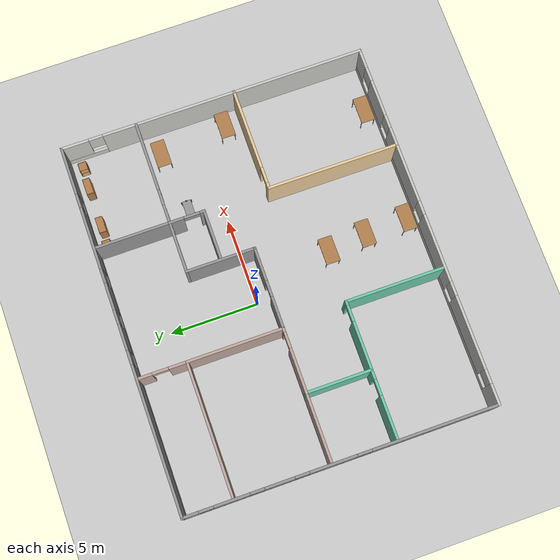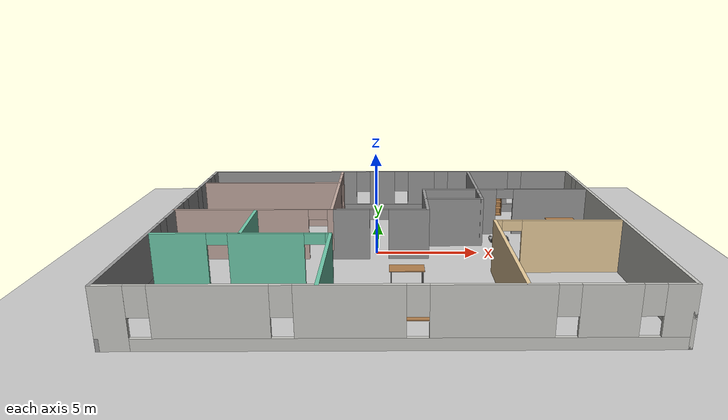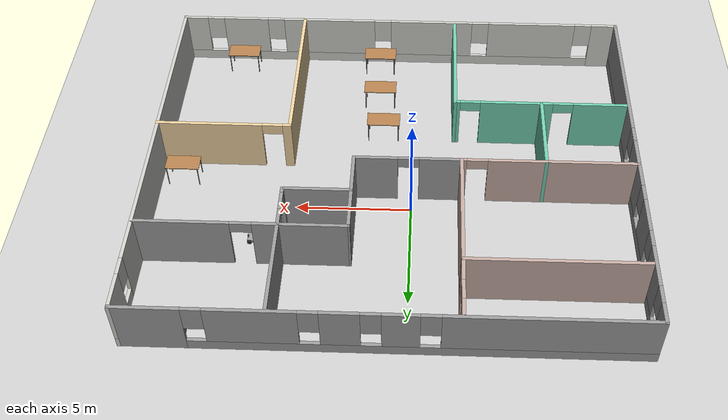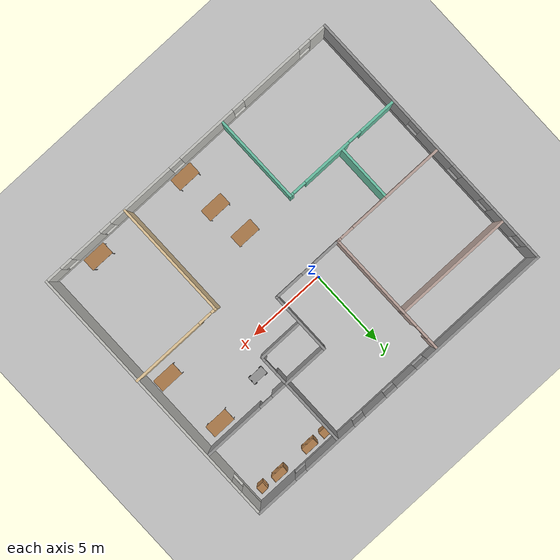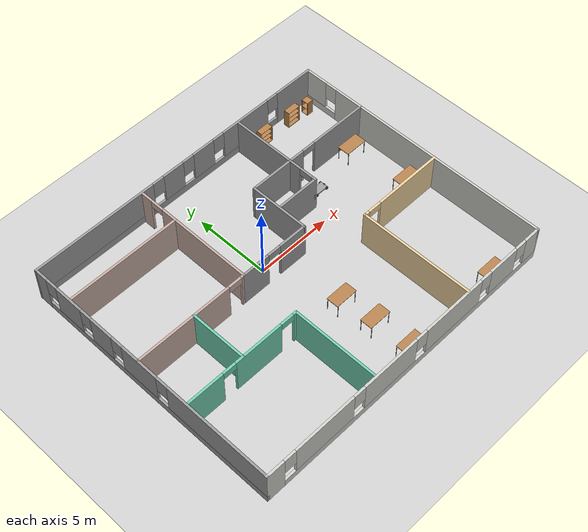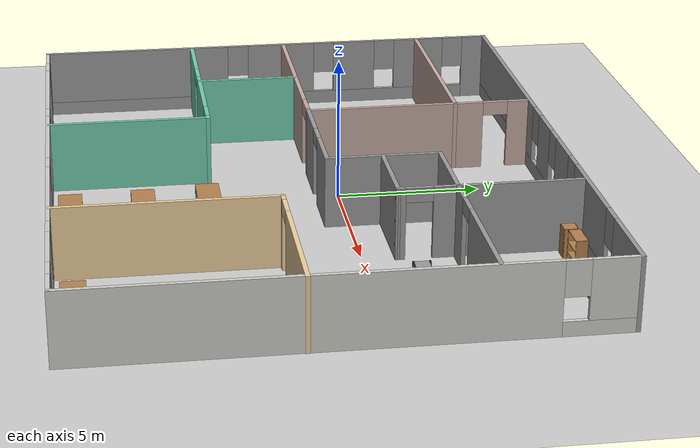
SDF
<sdf version="1.6">
 <world name="default">
  <plugin name="hello" filename="libhello.so"/>
  <light name="sun" type="directional">
   <pose>0 0 10 0 -0 0</pose>
   <diffuse>0.8 0.8 0.8 1</diffuse>
   <specular>0.2 0.2 0.2 1</specular>
   <attenuation>
    <range>1000</range>
    <constant>0.9</constant>
    <linear>0.01</linear>
    <quadratic>0.001</quadratic>
   </attenuation>
   <direction>-0.5 0.1 -0.9</direction>
  </light>
  <model name="ground_plane">
   <static>1</static>
   <link name="link">
    <collision name="collision">
     <geometry><plane><normal>0 0 1</normal><size>100 100</size></plane></geometry>
     <surface>
      <contact><collide_bitmask>65535</collide_bitmask></contact>
      <friction><ode><mu>100</mu><mu2>50</mu2></ode></friction>
     </surface>
    </collision>
    <visual name="visual">
     <cast_shadows>0</cast_shadows>
     <geometry><plane><normal>0 0 1</normal><size>100 100</size></plane></geometry>
     <material>
      <script><uri>file://media/materials/scripts/gazebo.material</uri><name>Gazebo/Grey</name></script>
     </material>
    </visual>
   </link>
  </model>
  <gravity>0 0 -9.8</gravity>
  <magnetic_field>6e-06 2.3e-05 -4.2e-05</magnetic_field>
  <atmosphere type="adiabatic"/>
  <physics name="default_physics" default="0" type="ode">
   <max_step_size>0.001</max_step_size>
   <real_time_factor>1</real_time_factor>
   <real_time_update_rate>1000</real_time_update_rate>
  </physics>
  <scene><ambient>0.4 0.4 0.4 1</ambient><background>0.7 0.7 0.7 1</background><shadows>1</shadows></scene>
  <spherical_coordinates>
   <surface_model>EARTH_WGS84</surface_model>
   <latitude_deg>0</latitude_deg>
   <longitude_deg>0</longitude_deg>
   <elevation>0</elevation>
   <heading_deg>0</heading_deg>
  </spherical_coordinates>
  <model name="Building">
   <pose>0.811073 -1.31925 0 0 -0 0</pose>
   <link name="Wall_1">
    <pose>-10.4348 0 0 0 0 -1.5708</pose>
    <visual name="Wall_1_Visual_0">
     <pose>-8.26713 0 1.25 0 -0 0</pose>
     <geometry><box><size>0.965742 0.15 2.5</size></box></geometry>
     <material>
      <script><uri>file://media/materials/scripts/gazebo.material</uri><name>Gazebo/Grey</name></script>
      <ambient>1 1 1 1</ambient>
     </material>
     <meta><layer>0</layer></meta>
    </visual>
    <collision name="Wall_1_Collision_0">
     <geometry><box><size>0.965742 0.15 2.5</size></box></geometry>
     <pose>-8.26713 0 1.25 0 -0 0</pose>
    </collision>
    <visual name="Wall_1_Visual_1">
     <pose>0.482871 0 0.25 0 -0 0</pose>
     <geometry><box><size>16.5343 0.15 0.5</size></box></geometry>
     <material>
      <script><uri>file://media/materials/scripts/gazebo.material</uri><name>Gazebo/Grey</name></script>
      <ambient>1 1 1 1</ambient>
     </material>
     <meta><layer>0</layer></meta>
    </visual>
    <collision name="Wall_1_Collision_1">
     <geometry><box><size>16.5343 0.15 0.5</size></box></geometry>
     <pose>0.482871 0 0.25 0 -0 0</pose>
    </collision>
    <visual name="Wall_1_Visual_2">
     <pose>-6.00096 0 1.5 0 -0 0</pose>
     <geometry><box><size>1.9666 0.15 2</size></box></geometry>
     <material>
      <script><uri>file://media/materials/scripts/gazebo.material</uri><name>Gazebo/Grey</name></script>
      <ambient>1 1 1 1</ambient>
     </material>
     <meta><layer>0</layer></meta>
    </visual>
    <collision name="Wall_1_Collision_2">
     <geometry><box><size>1.9666 0.15 2</size></box></geometry>
     <pose>-6.00096 0 1.5 0 -0 0</pose>
    </collision>
    <visual name="Wall_1_Visual_3">
     <pose>-3.3971 0 1.5 0 -0 0</pose>
     <geometry><box><size>1.64112 0.15 2</size></box></geometry>
     <material>
      <script><uri>file://media/materials/scripts/gazebo.material</uri><name>Gazebo/Grey</name></script>
      <ambient>1 1 1 1</ambient>
     </material>
     <meta><layer>0</layer></meta>
    </visual>
    <collision name="Wall_1_Collision_3">
     <geometry><box><size>1.64112 0.15 2</size></box></geometry>
     <pose>-3.3971 0 1.5 0 -0 0</pose>
    </collision>
    <visual name="Wall_1_Visual_4">
     <pose>-0.467756 0 1.5 0 -0 0</pose>
     <geometry><box><size>2.61757 0.15 2</size></box></geometry>
     <material>
      <script><uri>file://media/materials/scripts/gazebo.material</uri><name>Gazebo/Grey</name></script>
      <ambient>1 1 1 1</ambient>
     </material>
     <meta><layer>0</layer></meta>
    </visual>
    <collision name="Wall_1_Collision_4">
     <geometry><box><size>2.61757 0.15 2</size></box></geometry>
     <pose>-0.467756 0 1.5 0 -0 0</pose>
    </collision>
    <visual name="Wall_1_Visual_5">
     <pose>5.19551 0 1.5 0 -0 0</pose>
     <geometry><box><size>7.10897 0.15 2</size></box></geometry>
     <material>
      <script><uri>file://media/materials/scripts/gazebo.material</uri><name>Gazebo/Grey</name></script>
      <ambient>1 1 1 1</ambient>
     </material>
     <meta><layer>0</layer></meta>
    </visual>
    <collision name="Wall_1_Collision_5">
     <geometry><box><size>7.10897 0.15 2</size></box></geometry>
     <pose>5.19551 0 1.5 0 -0 0</pose>
    </collision>
    <visual name="Wall_1_Visual_6">
     <pose>-7.38426 0 1.9 0 -0 0</pose>
     <geometry><box><size>0.8 0.15 1.2</size></box></geometry>
     <material>
      <script><uri>file://media/materials/scripts/gazebo.material</uri><name>Gazebo/Grey</name></script>
      <ambient>1 1 1 1</ambient>
     </material>
     <meta><layer>0</layer></meta>
    </visual>
    <collision name="Wall_1_Collision_6">
     <geometry><box><size>0.8 0.15 1.2</size></box></geometry>
     <pose>-7.38426 0 1.9 0 -0 0</pose>
    </collision>
    <visual name="Wall_1_Visual_7">
     <pose>-4.61766 0 1.9 0 -0 0</pose>
     <geometry><box><size>0.8 0.15 1.2</size></box></geometry>
     <material>
      <script><uri>file://media/materials/scripts/gazebo.material</uri><name>Gazebo/Grey</name></script>
      <ambient>1 1 1 1</ambient>
     </material>
     <meta><layer>0</layer></meta>
    </visual>
    <collision name="Wall_1_Collision_7">
     <geometry><box><size>0.8 0.15 1.2</size></box></geometry>
     <pose>-4.61766 0 1.9 0 -0 0</pose>
    </collision>
    <visual name="Wall_1_Visual_8">
     <pose>-2.17654 0 1.9 0 -0 0</pose>
     <geometry><box><size>0.8 0.15 1.2</size></box></geometry>
     <material>
      <script><uri>file://media/materials/scripts/gazebo.material</uri><name>Gazebo/Grey</name></script>
      <ambient>1 1 1 1</ambient>
     </material>
     <meta><layer>0</layer></meta>
    </visual>
    <collision name="Wall_1_Collision_8">
     <geometry><box><size>0.8 0.15 1.2</size></box></geometry>
     <pose>-2.17654 0 1.9 0 -0 0</pose>
    </collision>
    <visual name="Wall_1_Visual_9">
     <pose>1.24103 0 1.9 0 -0 0</pose>
     <geometry><box><size>0.8 0.15 1.2</size></box></geometry>
     <material>
      <script><uri>file://media/materials/scripts/gazebo.material</uri><name>Gazebo/Grey</name></script>
      <ambient>1 1 1 1</ambient>
     </material>
     <meta><layer>0</layer></meta>
    </visual>
    <collision name="Wall_1_Collision_9">
     <geometry><box><size>0.8 0.15 1.2</size></box></geometry>
     <pose>1.24103 0 1.9 0 -0 0</pose>
    </collision>
   </link>
   <link name="Wall_10">
    <collision name="Wall_10_Collision">
     <geometry><box><size>4 0.15 2.5</size></box></geometry>
     <pose>0 0 1.25 0 -0 0</pose>
    </collision>
    <visual name="Wall_10_Visual">
     <pose>0 0 1.25 0 -0 0</pose>
     <geometry><box><size>4 0.15 2.5</size></box></geometry>
     <material>
      <script><uri>file://media/materials/scripts/gazebo.material</uri><name>Gazebo/Grey</name></script>
      <ambient>0.760784 0.662745 0.627451 1</ambient>
     </material>
     <meta><layer>0</layer></meta>
    </visual>
    <pose>-8.46331 0.559038 0 0 -0 3.14159</pose>
   </link>
   <link name="Wall_12">
    <pose>-4.73832 0.559038 0 0 -0 0</pose>
    <visual name="Wall_12_Visual_0">
     <pose>-0.592728 0 1.25 0 -0 0</pose>
     <geometry><box><size>2.56454 0.15 2.5</size></box></geometry>
     <material>
      <script><uri>file://media/materials/scripts/gazebo.material</uri><name>Gazebo/Grey</name></script>
      <ambient>0.760784 0.662745 0.627451 1</ambient>
     </material>
     <meta><layer>0</layer></meta>
    </visual>
    <collision name="Wall_12_Collision_0">
     <geometry><box><size>2.56454 0.15 2.5</size></box></geometry>
     <pose>-0.592728 0 1.25 0 -0 0</pose>
    </collision>
    <visual name="Wall_12_Visual_1">
     <pose>1.73227 0 1.25 0 -0 0</pose>
     <geometry><box><size>0.285456 0.15 2.5</size></box></geometry>
     <material>
      <script><uri>file://media/materials/scripts/gazebo.material</uri><name>Gazebo/Grey</name></script>
      <ambient>0.760784 0.662745 0.627451 1</ambient>
     </material>
     <meta><layer>0</layer></meta>
    </visual>
    <collision name="Wall_12_Collision_1">
     <geometry><box><size>0.285456 0.15 2.5</size></box></geometry>
     <pose>1.73227 0 1.25 0 -0 0</pose>
    </collision>
    <visual name="Wall_12_Visual_2">
     <pose>1.13954 0 2.25 0 -0 0</pose>
     <geometry><box><size>0.9 0.15 0.5</size></box></geometry>
     <material>
      <script><uri>file://media/materials/scripts/gazebo.material</uri><name>Gazebo/Grey</name></script>
      <ambient>0.760784 0.662745 0.627451 1</ambient>
     </material>
     <meta><layer>0</layer></meta>
    </visual>
    <collision name="Wall_12_Collision_2">
     <geometry><box><size>0.9 0.15 0.5</size></box></geometry>
     <pose>1.13954 0 2.25 0 -0 0</pose>
    </collision>
   </link>
   <link name="Wall_13">
    <collision name="Wall_13_Collision">
     <geometry><box><size>5.5 0.15 2.5</size></box></geometry>
     <pose>0 0 1.25 0 -0 0</pose>
    </collision>
    <visual name="Wall_13_Visual">
     <pose>0 0 1.25 0 -0 0</pose>
     <geometry><box><size>5.5 0.15 2.5</size></box></geometry>
     <material>
      <script><uri>file://media/materials/scripts/gazebo.material</uri><name>Gazebo/Grey</name></script>
      <ambient>0.760784 0.662745 0.627451 1</ambient>
     </material>
     <meta><layer>0</layer></meta>
    </visual>
    <pose>-2.93835 3.23415 0 0 -0 1.57081</pose>
   </link>
   <link name="Wall_14">
    <collision name="Wall_14_Collision">
     <geometry><box><size>7.5 0.15 2.5</size></box></geometry>
     <pose>0 0 1.25 0 -0 0</pose>
    </collision>
    <visual name="Wall_14_Visual">
     <pose>0 0 1.25 0 -0 0</pose>
     <geometry><box><size>7.5 0.15 2.5</size></box></geometry>
     <material>
      <script><uri>file://media/materials/scripts/gazebo.material</uri><name>Gazebo/Grey</name></script>
      <ambient>0.760784 0.662745 0.627451 1</ambient>
     </material>
     <meta><layer>0</layer></meta>
    </visual>
    <pose>-6.61335 5.90915 0 0 0 -3.14156</pose>
   </link>
   <link name="Wall_16">
    <pose>-2.93838 7.21526 0 0 -0 1.5708</pose>
    <visual name="Wall_16_Visual_0">
     <pose>-0.831001 0 1.25 0 -0 0</pose>
     <geometry><box><size>1.1 0.15 2.5</size></box></geometry>
     <material>
      <script><uri>file://media/materials/scripts/gazebo.material</uri><name>Gazebo/Grey</name></script>
      <ambient>0.760784 0.662745 0.627451 1</ambient>
     </material>
     <meta><layer>0</layer></meta>
    </visual>
    <collision name="Wall_16_Collision_0">
     <geometry><box><size>1.1 0.15 2.5</size></box></geometry>
     <pose>-0.831001 0 1.25 0 -0 0</pose>
    </collision>
    <visual name="Wall_16_Visual_1">
     <pose>0.999999 0 1.25 0 -0 0</pose>
     <geometry><box><size>0.762002 0.15 2.5</size></box></geometry>
     <material>
      <script><uri>file://media/materials/scripts/gazebo.material</uri><name>Gazebo/Grey</name></script>
      <ambient>0.760784 0.662745 0.627451 1</ambient>
     </material>
     <meta><layer>0</layer></meta>
    </visual>
    <collision name="Wall_16_Collision_1">
     <geometry><box><size>0.762002 0.15 2.5</size></box></geometry>
     <pose>0.999999 0 1.25 0 -0 0</pose>
    </collision>
    <visual name="Wall_16_Visual_2">
     <pose>0.168998 0 2.25 0 -0 0</pose>
     <geometry><box><size>0.9 0.15 0.5</size></box></geometry>
     <material>
      <script><uri>file://media/materials/scripts/gazebo.material</uri><name>Gazebo/Grey</name></script>
      <ambient>0.760784 0.662745 0.627451 1</ambient>
     </material>
     <meta><layer>0</layer></meta>
    </visual>
    <collision name="Wall_16_Collision_2">
     <geometry><box><size>0.9 0.15 0.5</size></box></geometry>
     <pose>0.168998 0 2.25 0 -0 0</pose>
    </collision>
   </link>
   <link name="Wall_18">
    <collision name="Wall_18_Collision">
     <geometry><box><size>7.5 0.15 2.5</size></box></geometry>
     <pose>0 0 1.25 0 -0 0</pose>
    </collision>
    <visual name="Wall_18_Visual">
     <pose>0 0 1.25 0 -0 0</pose>
     <geometry><box><size>7.5 0.15 2.5</size></box></geometry>
     <material>
      <script><uri>file://media/materials/scripts/gazebo.material</uri><name>Gazebo/Grey</name></script>
      <ambient>0.921569 0.807843 0.615686 1</ambient>
     </material>
     <meta><layer>0</layer></meta>
    </visual>
    <pose>4.58481 -4.95144 0 0 -0 1.5708</pose>
   </link>
   <link name="Wall_19">
    <pose>7.50981 -1.27643 0 0 -0 0</pose>
    <visual name="Wall_19_Visual_0">
     <pose>-2.8039 0 1.25 0 -0 0</pose>
     <geometry><box><size>0.39219 0.15 2.5</size></box></geometry>
     <material>
      <script><uri>file://media/materials/scripts/gazebo.material</uri><name>Gazebo/Grey</name></script>
      <ambient>0.921569 0.807843 0.615686 1</ambient>
     </material>
     <meta><layer>0</layer></meta>
    </visual>
    <collision name="Wall_19_Collision_0">
     <geometry><box><size>0.39219 0.15 2.5</size></box></geometry>
     <pose>-2.8039 0 1.25 0 -0 0</pose>
    </collision>
    <visual name="Wall_19_Visual_1">
     <pose>0.646095 0 1.25 0 -0 0</pose>
     <geometry><box><size>4.70781 0.15 2.5</size></box></geometry>
     <material>
      <script><uri>file://media/materials/scripts/gazebo.material</uri><name>Gazebo/Grey</name></script>
      <ambient>0.921569 0.807843 0.615686 1</ambient>
     </material>
     <meta><layer>0</layer></meta>
    </visual>
    <collision name="Wall_19_Collision_1">
     <geometry><box><size>4.70781 0.15 2.5</size></box></geometry>
     <pose>0.646095 0 1.25 0 -0 0</pose>
    </collision>
    <visual name="Wall_19_Visual_2">
     <pose>-2.15781 0 2.25 0 -0 0</pose>
     <geometry><box><size>0.9 0.15 0.5</size></box></geometry>
     <material>
      <script><uri>file://media/materials/scripts/gazebo.material</uri><name>Gazebo/Grey</name></script>
      <ambient>0.921569 0.807843 0.615686 1</ambient>
     </material>
     <meta><layer>0</layer></meta>
    </visual>
    <collision name="Wall_19_Collision_2">
     <geometry><box><size>0.9 0.15 0.5</size></box></geometry>
     <pose>-2.15781 0 2.25 0 -0 0</pose>
    </collision>
   </link>
   <link name="Wall_2">
    <pose>-0.009806 -8.675 0 0 -0 0</pose>
    <visual name="Wall_2_Visual_0">
     <pose>-9.88903 0 1.25 0 -0 0</pose>
     <geometry><box><size>1.22195 0.15 2.5</size></box></geometry>
     <material>
      <script><uri>file://media/materials/scripts/gazebo.material</uri><name>Gazebo/CeilingTiled</name></script>
      <ambient>1 1 1 1</ambient>
     </material>
     <meta><layer>0</layer></meta>
    </visual>
    <collision name="Wall_2_Collision_0">
     <geometry><box><size>1.22195 0.15 2.5</size></box></geometry>
     <pose>-9.88903 0 1.25 0 -0 0</pose>
    </collision>
    <visual name="Wall_2_Visual_1">
     <pose>0.610973 0 0.25 0 -0 0</pose>
     <geometry><box><size>19.7781 0.15 0.5</size></box></geometry>
     <material>
      <script><uri>file://media/materials/scripts/gazebo.material</uri><name>Gazebo/CeilingTiled</name></script>
      <ambient>1 1 1 1</ambient>
     </material>
     <meta><layer>0</layer></meta>
    </visual>
    <collision name="Wall_2_Collision_1">
     <geometry><box><size>19.7781 0.15 0.5</size></box></geometry>
     <pose>0.610973 0 0.25 0 -0 0</pose>
    </collision>
    <visual name="Wall_2_Visual_2">
     <pose>-6.39625 0 1.5 0 -0 0</pose>
     <geometry><box><size>4.16361 0.15 2</size></box></geometry>
     <material>
      <script><uri>file://media/materials/scripts/gazebo.material</uri><name>Gazebo/CeilingTiled</name></script>
      <ambient>1 1 1 1</ambient>
     </material>
     <meta><layer>0</layer></meta>
    </visual>
    <collision name="Wall_2_Collision_2">
     <geometry><box><size>4.16361 0.15 2</size></box></geometry>
     <pose>-6.39625 0 1.5 0 -0 0</pose>
    </collision>
    <visual name="Wall_2_Visual_3">
     <pose>-1.5547 0 1.5 0 -0 0</pose>
     <geometry><box><size>3.9195 0.15 2</size></box></geometry>
     <material>
      <script><uri>file://media/materials/scripts/gazebo.material</uri><name>Gazebo/CeilingTiled</name></script>
      <ambient>1 1 1 1</ambient>
     </material>
     <meta><layer>0</layer></meta>
    </visual>
    <collision name="Wall_2_Collision_3">
     <geometry><box><size>3.9195 0.15 2</size></box></geometry>
     <pose>-1.5547 0 1.5 0 -0 0</pose>
    </collision>
    <visual name="Wall_2_Visual_4">
     <pose>3.40891 0 1.5 0 -0 0</pose>
     <geometry><box><size>4.40772 0.15 2</size></box></geometry>
     <material>
      <script><uri>file://media/materials/scripts/gazebo.material</uri><name>Gazebo/CeilingTiled</name></script>
      <ambient>1 1 1 1</ambient>
     </material>
     <meta><layer>0</layer></meta>
    </visual>
    <collision name="Wall_2_Collision_4">
     <geometry><box><size>4.40772 0.15 2</size></box></geometry>
     <pose>3.40891 0 1.5 0 -0 0</pose>
    </collision>
    <visual name="Wall_2_Visual_5">
     <pose>7.47744 0 1.5 0 -0 0</pose>
     <geometry><box><size>2.12934 0.15 2</size></box></geometry>
     <material>
      <script><uri>file://media/materials/scripts/gazebo.material</uri><name>Gazebo/CeilingTiled</name></script>
      <ambient>1 1 1 1</ambient>
     </material>
     <meta><layer>0</layer></meta>
    </visual>
    <collision name="Wall_2_Collision_5">
     <geometry><box><size>2.12934 0.15 2</size></box></geometry>
     <pose>7.47744 0 1.5 0 -0 0</pose>
    </collision>
    <visual name="Wall_2_Visual_6">
     <pose>9.92106 0 1.5 0 -0 0</pose>
     <geometry><box><size>1.15789 0.15 2</size></box></geometry>
     <material>
      <script><uri>file://media/materials/scripts/gazebo.material</uri><name>Gazebo/CeilingTiled</name></script>
      <ambient>1 1 1 1</ambient>
     </material>
     <meta><layer>0</layer></meta>
    </visual>
    <collision name="Wall_2_Collision_6">
     <geometry><box><size>1.15789 0.15 2</size></box></geometry>
     <pose>9.92106 0 1.5 0 -0 0</pose>
    </collision>
    <visual name="Wall_2_Visual_7">
     <pose>-8.87805 0 1.9 0 -0 0</pose>
     <geometry><box><size>0.8 0.15 1.2</size></box></geometry>
     <material>
      <script><uri>file://media/materials/scripts/gazebo.material</uri><name>Gazebo/CeilingTiled</name></script>
      <ambient>1 1 1 1</ambient>
     </material>
     <meta><layer>0</layer></meta>
    </visual>
    <collision name="Wall_2_Collision_7">
     <geometry><box><size>0.8 0.15 1.2</size></box></geometry>
     <pose>-8.87805 0 1.9 0 -0 0</pose>
    </collision>
    <visual name="Wall_2_Visual_8">
     <pose>-3.91445 0 1.9 0 -0 0</pose>
     <geometry><box><size>0.8 0.15 1.2</size></box></geometry>
     <material>
      <script><uri>file://media/materials/scripts/gazebo.material</uri><name>Gazebo/CeilingTiled</name></script>
      <ambient>1 1 1 1</ambient>
     </material>
     <meta><layer>0</layer></meta>
    </visual>
    <collision name="Wall_2_Collision_8">
     <geometry><box><size>0.8 0.15 1.2</size></box></geometry>
     <pose>-3.91445 0 1.9 0 -0 0</pose>
    </collision>
    <visual name="Wall_2_Visual_9">
     <pose>0.805049 0 1.9 0 -0 0</pose>
     <geometry><box><size>0.8 0.15 1.2</size></box></geometry>
     <material>
      <script><uri>file://media/materials/scripts/gazebo.material</uri><name>Gazebo/CeilingTiled</name></script>
      <ambient>1 1 1 1</ambient>
     </material>
     <meta><layer>0</layer></meta>
    </visual>
    <collision name="Wall_2_Collision_9">
     <geometry><box><size>0.8 0.15 1.2</size></box></geometry>
     <pose>0.805049 0 1.9 0 -0 0</pose>
    </collision>
    <visual name="Wall_2_Visual_10">
     <pose>6.01277 0 1.9 0 -0 0</pose>
     <geometry><box><size>0.8 0.15 1.2</size></box></geometry>
     <material>
      <script><uri>file://media/materials/scripts/gazebo.material</uri><name>Gazebo/CeilingTiled</name></script>
      <ambient>1 1 1 1</ambient>
     </material>
     <meta><layer>0</layer></meta>
    </visual>
    <collision name="Wall_2_Collision_10">
     <geometry><box><size>0.8 0.15 1.2</size></box></geometry>
     <pose>6.01277 0 1.9 0 -0 0</pose>
    </collision>
    <visual name="Wall_2_Visual_11">
     <pose>8.94211 0 1.9 0 -0 0</pose>
     <geometry><box><size>0.8 0.15 1.2</size></box></geometry>
     <material>
      <script><uri>file://media/materials/scripts/gazebo.material</uri><name>Gazebo/CeilingTiled</name></script>
      <ambient>1 1 1 1</ambient>
     </material>
     <meta><layer>0</layer></meta>
    </visual>
    <collision name="Wall_2_Collision_11">
     <geometry><box><size>0.8 0.15 1.2</size></box></geometry>
     <pose>8.94211 0 1.9 0 -0 0</pose>
    </collision>
   </link>
   <link name="Wall_21">
    <pose>-0.638315 0.559038 0 0 -0 0</pose>
    <visual name="Wall_21_Visual_0">
     <pose>-1.42806 0 1.25 0 -0 0</pose>
     <geometry><box><size>1.89389 0.15 2.5</size></box></geometry>
     <material>
      <script><uri>file://media/materials/scripts/gazebo.material</uri><name>Gazebo/Grey</name></script>
      <ambient>1 1 1 1</ambient>
     </material>
     <meta><layer>0</layer></meta>
    </visual>
    <collision name="Wall_21_Collision_0">
     <geometry><box><size>1.89389 0.15 2.5</size></box></geometry>
     <pose>-1.42806 0 1.25 0 -0 0</pose>
    </collision>
    <visual name="Wall_21_Visual_1">
     <pose>1.39694 0 1.25 0 -0 0</pose>
     <geometry><box><size>1.95611 0.15 2.5</size></box></geometry>
     <material>
      <script><uri>file://media/materials/scripts/gazebo.material</uri><name>Gazebo/Grey</name></script>
      <ambient>1 1 1 1</ambient>
     </material>
     <meta><layer>0</layer></meta>
    </visual>
    <collision name="Wall_21_Collision_1">
     <geometry><box><size>1.95611 0.15 2.5</size></box></geometry>
     <pose>1.39694 0 1.25 0 -0 0</pose>
    </collision>
    <visual name="Wall_21_Visual_2">
     <pose>-0.031114 0 2.25 0 -0 0</pose>
     <geometry><box><size>0.9 0.15 0.5</size></box></geometry>
     <material>
      <script><uri>file://media/materials/scripts/gazebo.material</uri><name>Gazebo/Grey</name></script>
      <ambient>1 1 1 1</ambient>
     </material>
     <meta><layer>0</layer></meta>
    </visual>
    <collision name="Wall_21_Collision_2">
     <geometry><box><size>0.9 0.15 0.5</size></box></geometry>
     <pose>-0.031114 0 2.25 0 -0 0</pose>
    </collision>
   </link>
   <link name="Wall_22">
    <collision name="Wall_22_Collision">
     <geometry><box><size>4 0.15 2.5</size></box></geometry>
     <pose>0 0 1.25 0 -0 0</pose>
    </collision>
    <visual name="Wall_22_Visual">
     <pose>0 0 1.25 0 -0 0</pose>
     <geometry><box><size>4 0.15 2.5</size></box></geometry>
     <material>
      <script><uri>file://media/materials/scripts/gazebo.material</uri><name>Gazebo/Grey</name></script>
      <ambient>1 1 1 1</ambient>
     </material>
     <meta><layer>0</layer></meta>
    </visual>
    <pose>1.66169 2.48404 0 0 -0 1.5708</pose>
   </link>
   <link name="Wall_23">
    <collision name="Wall_23_Collision">
     <geometry><box><size>3 0.15 2.5</size></box></geometry>
     <pose>0 0 1.25 0 -0 0</pose>
    </collision>
    <visual name="Wall_23_Visual">
     <pose>0 0 1.25 0 -0 0</pose>
     <geometry><box><size>3 0.15 2.5</size></box></geometry>
     <material>
      <script><uri>file://media/materials/scripts/gazebo.material</uri><name>Gazebo/Grey</name></script>
      <ambient>1 1 1 1</ambient>
     </material>
     <meta><layer>0</layer></meta>
    </visual>
    <pose>3.08665 4.40915 0 0 -0 7.8e-05</pose>
   </link>
   <link name="Wall_24">
    <collision name="Wall_24_Collision">
     <geometry><box><size>4.268 0.15 2.5</size></box></geometry>
     <pose>0 0 1.25 0 -0 0</pose>
    </collision>
    <visual name="Wall_24_Visual">
     <pose>0 0 1.25 0 -0 0</pose>
     <geometry><box><size>4.268 0.15 2.5</size></box></geometry>
     <material>
      <script><uri>file://media/materials/scripts/gazebo.material</uri><name>Gazebo/Grey</name></script>
      <ambient>0 0 0 1</ambient>
     </material>
     <meta><layer>0</layer></meta>
    </visual>
    <pose>4.51162 6.46826 0 0 -0 1.5708</pose>
   </link>
   <link name="Wall_29">
    <collision name="Wall_29_Collision">
     <geometry><box><size>3 0.15 2.5</size></box></geometry>
     <pose>0 0 1.25 0 -0 0</pose>
    </collision>
    <visual name="Wall_29_Visual">
     <pose>0 0 1.25 0 -0 0</pose>
     <geometry><box><size>3 0.15 2.5</size></box></geometry>
     <material>
      <script><uri>file://media/materials/scripts/gazebo.material</uri><name>Gazebo/Grey</name></script>
      <ambient>1 1 1 1</ambient>
     </material>
     <meta><layer>0</layer></meta>
    </visual>
    <pose>3.09 2.4505 0 0 -0 0</pose>
   </link>
   <link name="Wall_3">
    <pose>10.4152 0 0 0 -0 1.5708</pose>
    <visual name="Wall_3_Visual_0">
     <pose>-1.20835 0 1.25 0 -0 0</pose>
     <geometry><box><size>15.0833 0.15 2.5</size></box></geometry>
     <material>
      <script><uri>file://media/materials/scripts/gazebo.material</uri><name>Gazebo/CeilingTiled</name></script>
      <ambient>1 1 1 1</ambient>
     </material>
     <meta><layer>0</layer></meta>
    </visual>
    <collision name="Wall_3_Collision_0">
     <geometry><box><size>15.0833 0.15 2.5</size></box></geometry>
     <pose>-1.20835 0 1.25 0 -0 0</pose>
    </collision>
    <visual name="Wall_3_Visual_1">
     <pose>7.54165 0 0.25 0 -0 0</pose>
     <geometry><box><size>2.41671 0.15 0.5</size></box></geometry>
     <material>
      <script><uri>file://media/materials/scripts/gazebo.material</uri><name>Gazebo/CeilingTiled</name></script>
      <ambient>1 1 1 1</ambient>
     </material>
     <meta><layer>0</layer></meta>
    </visual>
    <collision name="Wall_3_Collision_1">
     <geometry><box><size>2.41671 0.15 0.5</size></box></geometry>
     <pose>7.54165 0 0.25 0 -0 0</pose>
    </collision>
    <visual name="Wall_3_Visual_2">
     <pose>7.94165 0 1.5 0 -0 0</pose>
     <geometry><box><size>1.61671 0.15 2</size></box></geometry>
     <material>
      <script><uri>file://media/materials/scripts/gazebo.material</uri><name>Gazebo/CeilingTiled</name></script>
      <ambient>1 1 1 1</ambient>
     </material>
     <meta><layer>0</layer></meta>
    </visual>
    <collision name="Wall_3_Collision_2">
     <geometry><box><size>1.61671 0.15 2</size></box></geometry>
     <pose>7.94165 0 1.5 0 -0 0</pose>
    </collision>
    <visual name="Wall_3_Visual_3">
     <pose>6.73329 0 1.9 0 -0 0</pose>
     <geometry><box><size>0.8 0.15 1.2</size></box></geometry>
     <material>
      <script><uri>file://media/materials/scripts/gazebo.material</uri><name>Gazebo/CeilingTiled</name></script>
      <ambient>1 1 1 1</ambient>
     </material>
     <meta><layer>0</layer></meta>
    </visual>
    <collision name="Wall_3_Collision_3">
     <geometry><box><size>0.8 0.15 1.2</size></box></geometry>
     <pose>6.73329 0 1.9 0 -0 0</pose>
    </collision>
   </link>
   <link name="Wall_30">
    <pose>4.51331 3.42988 0 0 -0 1.57252</pose>
    <visual name="Wall_30_Visual_0">
     <pose>-0.890603 0 1.25 0 -0 0</pose>
     <geometry><box><size>0.327334 0.15 2.5</size></box></geometry>
     <material>
      <script><uri>file://media/materials/scripts/gazebo.material</uri><name>Gazebo/Grey</name></script>
      <ambient>1 1 1 1</ambient>
     </material>
     <meta><layer>0</layer></meta>
    </visual>
    <collision name="Wall_30_Collision_0">
     <geometry><box><size>0.327334 0.15 2.5</size></box></geometry>
     <pose>-0.890603 0 1.25 0 -0 0</pose>
    </collision>
    <visual name="Wall_30_Visual_1">
     <pose>0.613667 0 1.25 0 -0 0</pose>
     <geometry><box><size>0.881207 0.15 2.5</size></box></geometry>
     <material>
      <script><uri>file://media/materials/scripts/gazebo.material</uri><name>Gazebo/Grey</name></script>
      <ambient>1 1 1 1</ambient>
     </material>
     <meta><layer>0</layer></meta>
    </visual>
    <collision name="Wall_30_Collision_1">
     <geometry><box><size>0.881207 0.15 2.5</size></box></geometry>
     <pose>0.613667 0 1.25 0 -0 0</pose>
    </collision>
    <visual name="Wall_30_Visual_2">
     <pose>-0.276937 0 2.25 0 -0 0</pose>
     <geometry><box><size>0.9 0.15 0.5</size></box></geometry>
     <material>
      <script><uri>file://media/materials/scripts/gazebo.material</uri><name>Gazebo/Grey</name></script>
      <ambient>1 1 1 1</ambient>
     </material>
     <meta><layer>0</layer></meta>
    </visual>
    <collision name="Wall_30_Collision_2">
     <geometry><box><size>0.9 0.15 0.5</size></box></geometry>
     <pose>-0.276937 0 2.25 0 -0 0</pose>
    </collision>
   </link>
   <link name="Wall_32">
    <pose>7.43665 4.40915 0 0 0 -3.8e-05</pose>
    <visual name="Wall_32_Visual_0">
     <pose>-2.44184 0 1.25 0 -0 0</pose>
     <geometry><box><size>1.11631 0.15 2.5</size></box></geometry>
     <material>
      <script><uri>file://media/materials/scripts/gazebo.material</uri><name>Gazebo/Grey</name></script>
      <ambient>0 0 0 1</ambient>
     </material>
     <meta><layer>0</layer></meta>
    </visual>
    <collision name="Wall_32_Collision_0">
     <geometry><box><size>1.11631 0.15 2.5</size></box></geometry>
     <pose>-2.44184 0 1.25 0 -0 0</pose>
    </collision>
    <visual name="Wall_32_Visual_1">
     <pose>1.00815 0 1.25 0 -0 0</pose>
     <geometry><box><size>3.98369 0.15 2.5</size></box></geometry>
     <material>
      <script><uri>file://media/materials/scripts/gazebo.material</uri><name>Gazebo/Grey</name></script>
      <ambient>0 0 0 1</ambient>
     </material>
     <meta><layer>0</layer></meta>
    </visual>
    <collision name="Wall_32_Collision_1">
     <geometry><box><size>3.98369 0.15 2.5</size></box></geometry>
     <pose>1.00815 0 1.25 0 -0 0</pose>
    </collision>
    <visual name="Wall_32_Visual_2">
     <pose>-1.43369 0 2.25 0 -0 0</pose>
     <geometry><box><size>0.9 0.15 0.5</size></box></geometry>
     <material>
      <script><uri>file://media/materials/scripts/gazebo.material</uri><name>Gazebo/Grey</name></script>
      <ambient>0 0 0 1</ambient>
     </material>
     <meta><layer>0</layer></meta>
    </visual>
    <collision name="Wall_32_Collision_2">
     <geometry><box><size>0.9 0.15 0.5</size></box></geometry>
     <pose>-1.43369 0 2.25 0 -0 0</pose>
    </collision>
   </link>
   <link name="Wall_4">
    <pose>-0.009806 8.675 0 0 -0 3.14159</pose>
    <visual name="Wall_4_Visual_0">
     <pose>-9.10735 0 1.25 0 -0 0</pose>
     <geometry><box><size>2.7853 0.15 2.5</size></box></geometry>
     <material>
      <script><uri>file://media/materials/scripts/gazebo.material</uri><name>Gazebo/Grey</name></script>
      <ambient>1 1 1 1</ambient>
     </material>
     <meta><layer>0</layer></meta>
    </visual>
    <collision name="Wall_4_Collision_0">
     <geometry><box><size>2.7853 0.15 2.5</size></box></geometry>
     <pose>-9.10735 0 1.25 0 -0 0</pose>
    </collision>
    <visual name="Wall_4_Visual_1">
     <pose>1.39265 0 0.25 0 -0 0</pose>
     <geometry><box><size>18.2147 0.15 0.5</size></box></geometry>
     <material>
      <script><uri>file://media/materials/scripts/gazebo.material</uri><name>Gazebo/Grey</name></script>
      <ambient>1 1 1 1</ambient>
     </material>
     <meta><layer>0</layer></meta>
    </visual>
    <collision name="Wall_4_Collision_1">
     <geometry><box><size>18.2147 0.15 0.5</size></box></geometry>
     <pose>1.39265 0 0.25 0 -0 0</pose>
    </collision>
    <visual name="Wall_4_Visual_2">
     <pose>-5.11769 0 1.5 0 -0 0</pose>
     <geometry><box><size>3.59401 0.15 2</size></box></geometry>
     <material>
      <script><uri>file://media/materials/scripts/gazebo.material</uri><name>Gazebo/Grey</name></script>
      <ambient>1 1 1 1</ambient>
     </material>
     <meta><layer>0</layer></meta>
    </visual>
    <collision name="Wall_4_Collision_2">
     <geometry><box><size>3.59401 0.15 2</size></box></geometry>
     <pose>-5.11769 0 1.5 0 -0 0</pose>
    </collision>
    <visual name="Wall_4_Visual_3">
     <pose>-1.74081 0 1.5 0 -0 0</pose>
     <geometry><box><size>1.55975 0.15 2</size></box></geometry>
     <material>
      <script><uri>file://media/materials/scripts/gazebo.material</uri><name>Gazebo/Grey</name></script>
      <ambient>1 1 1 1</ambient>
     </material>
     <meta><layer>0</layer></meta>
    </visual>
    <collision name="Wall_4_Collision_3">
     <geometry><box><size>1.55975 0.15 2</size></box></geometry>
     <pose>-1.74081 0 1.5 0 -0 0</pose>
    </collision>
    <visual name="Wall_4_Visual_4">
     <pose>0.578252 0 1.5 0 -0 0</pose>
     <geometry><box><size>1.47838 0.15 2</size></box></geometry>
     <material>
      <script><uri>file://media/materials/scripts/gazebo.material</uri><name>Gazebo/Grey</name></script>
      <ambient>1 1 1 1</ambient>
     </material>
     <meta><layer>0</layer></meta>
    </visual>
    <collision name="Wall_4_Collision_4">
     <geometry><box><size>1.47838 0.15 2</size></box></geometry>
     <pose>0.578252 0 1.5 0 -0 0</pose>
    </collision>
    <visual name="Wall_4_Visual_5">
     <pose>6.30872 0 1.5 0 -0 0</pose>
     <geometry><box><size>8.38256 0.15 2</size></box></geometry>
     <material>
      <script><uri>file://media/materials/scripts/gazebo.material</uri><name>Gazebo/Grey</name></script>
      <ambient>1 1 1 1</ambient>
     </material>
     <meta><layer>0</layer></meta>
    </visual>
    <collision name="Wall_4_Collision_5">
     <geometry><box><size>8.38256 0.15 2</size></box></geometry>
     <pose>6.30872 0 1.5 0 -0 0</pose>
    </collision>
    <visual name="Wall_4_Visual_6">
     <pose>-7.3147 0 1.9 0 -0 0</pose>
     <geometry><box><size>0.8 0.15 1.2</size></box></geometry>
     <material>
      <script><uri>file://media/materials/scripts/gazebo.material</uri><name>Gazebo/Grey</name></script>
      <ambient>1 1 1 1</ambient>
     </material>
     <meta><layer>0</layer></meta>
    </visual>
    <collision name="Wall_4_Collision_6">
     <geometry><box><size>0.8 0.15 1.2</size></box></geometry>
     <pose>-7.3147 0 1.9 0 -0 0</pose>
    </collision>
    <visual name="Wall_4_Visual_7">
     <pose>-2.92069 0 1.9 0 -0 0</pose>
     <geometry><box><size>0.8 0.15 1.2</size></box></geometry>
     <material>
      <script><uri>file://media/materials/scripts/gazebo.material</uri><name>Gazebo/Grey</name></script>
      <ambient>1 1 1 1</ambient>
     </material>
     <meta><layer>0</layer></meta>
    </visual>
    <collision name="Wall_4_Collision_7">
     <geometry><box><size>0.8 0.15 1.2</size></box></geometry>
     <pose>-2.92069 0 1.9 0 -0 0</pose>
    </collision>
    <visual name="Wall_4_Visual_8">
     <pose>-0.560937 0 1.9 0 -0 0</pose>
     <geometry><box><size>0.8 0.15 1.2</size></box></geometry>
     <material>
      <script><uri>file://media/materials/scripts/gazebo.material</uri><name>Gazebo/Grey</name></script>
      <ambient>1 1 1 1</ambient>
     </material>
     <meta><layer>0</layer></meta>
    </visual>
    <collision name="Wall_4_Collision_8">
     <geometry><box><size>0.8 0.15 1.2</size></box></geometry>
     <pose>-0.560937 0 1.9 0 -0 0</pose>
    </collision>
    <visual name="Wall_4_Visual_9">
     <pose>1.71744 0 1.9 0 -0 0</pose>
     <geometry><box><size>0.8 0.15 1.2</size></box></geometry>
     <material>
      <script><uri>file://media/materials/scripts/gazebo.material</uri><name>Gazebo/Grey</name></script>
      <ambient>1 1 1 1</ambient>
     </material>
     <meta><layer>0</layer></meta>
    </visual>
    <collision name="Wall_4_Collision_9">
     <geometry><box><size>0.8 0.15 1.2</size></box></geometry>
     <pose>1.71744 0 1.9 0 -0 0</pose>
    </collision>
   </link>
   <link name="Wall_6">
    <collision name="Wall_6_Collision">
     <geometry><box><size>5.75 0.15 2.5</size></box></geometry>
     <pose>0 0 1.25 0 -0 0</pose>
    </collision>
    <visual name="Wall_6_Visual">
     <pose>0 0 1.25 0 -0 0</pose>
     <geometry><box><size>5.75 0.15 2.5</size></box></geometry>
     <material>
      <script><uri>file://media/materials/scripts/gazebo.material</uri><name>Gazebo/Grey</name></script>
      <ambient>0.435294 0.796078 0.67451 1</ambient>
     </material>
     <meta><layer>0</layer></meta>
    </visual>
    <pose>-2.68597 -5.85697 0 0 -0 1.5708</pose>
   </link>
   <link name="Wall_7">
    <pose>-6.48597 -3.05697 0 0 -0 3.14159</pose>
    <visual name="Wall_7_Visual_0">
     <pose>-3.72816 0 1.25 0 -0 0</pose>
     <geometry><box><size>0.293686 0.15 2.5</size></box></geometry>
     <material>
      <script><uri>file://media/materials/scripts/gazebo.material</uri><name>Gazebo/Grey</name></script>
      <ambient>0.435294 0.796078 0.67451 1</ambient>
     </material>
     <meta><layer>0</layer></meta>
    </visual>
    <collision name="Wall_7_Collision_0">
     <geometry><box><size>0.293686 0.15 2.5</size></box></geometry>
     <pose>-3.72816 0 1.25 0 -0 0</pose>
    </collision>
    <visual name="Wall_7_Visual_1">
     <pose>-1.05636 0 1.25 0 -0 0</pose>
     <geometry><box><size>3.2499 0.15 2.5</size></box></geometry>
     <material>
      <script><uri>file://media/materials/scripts/gazebo.material</uri><name>Gazebo/Grey</name></script>
      <ambient>0.435294 0.796078 0.67451 1</ambient>
     </material>
     <meta><layer>0</layer></meta>
    </visual>
    <collision name="Wall_7_Collision_1">
     <geometry><box><size>3.2499 0.15 2.5</size></box></geometry>
     <pose>-1.05636 0 1.25 0 -0 0</pose>
    </collision>
    <visual name="Wall_7_Visual_2">
     <pose>2.67179 0 1.25 0 -0 0</pose>
     <geometry><box><size>2.40641 0.15 2.5</size></box></geometry>
     <material>
      <script><uri>file://media/materials/scripts/gazebo.material</uri><name>Gazebo/Grey</name></script>
      <ambient>0.435294 0.796078 0.67451 1</ambient>
     </material>
     <meta><layer>0</layer></meta>
    </visual>
    <collision name="Wall_7_Collision_2">
     <geometry><box><size>2.40641 0.15 2.5</size></box></geometry>
     <pose>2.67179 0 1.25 0 -0 0</pose>
    </collision>
    <visual name="Wall_7_Visual_3">
     <pose>-3.13131 0 2.25 0 -0 0</pose>
     <geometry><box><size>0.9 0.15 0.5</size></box></geometry>
     <material>
      <script><uri>file://media/materials/scripts/gazebo.material</uri><name>Gazebo/Grey</name></script>
      <ambient>0.435294 0.796078 0.67451 1</ambient>
     </material>
     <meta><layer>0</layer></meta>
    </visual>
    <collision name="Wall_7_Collision_3">
     <geometry><box><size>0.9 0.15 0.5</size></box></geometry>
     <pose>-3.13131 0 2.25 0 -0 0</pose>
    </collision>
    <visual name="Wall_7_Visual_4">
     <pose>1.01859 0 2.25 0 -0 0</pose>
     <geometry><box><size>0.9 0.15 0.5</size></box></geometry>
     <material>
      <script><uri>file://media/materials/scripts/gazebo.material</uri><name>Gazebo/Grey</name></script>
      <ambient>0.435294 0.796078 0.67451 1</ambient>
     </material>
     <meta><layer>0</layer></meta>
    </visual>
    <collision name="Wall_7_Collision_4">
     <geometry><box><size>0.9 0.15 0.5</size></box></geometry>
     <pose>1.01859 0 2.25 0 -0 0</pose>
    </collision>
   </link>
   <link name="Wall_9">
    <collision name="Wall_9_Collision">
     <geometry><box><size>3.75 0.15 2.5</size></box></geometry>
     <pose>0 0 1.25 0 -0 0</pose>
    </collision>
    <visual name="Wall_9_Visual">
     <pose>0 0 1.25 0 -0 0</pose>
     <geometry><box><size>3.75 0.15 2.5</size></box></geometry>
     <material>
      <script><uri>file://media/materials/scripts/gazebo.material</uri><name>Gazebo/Grey</name></script>
      <ambient>0.435294 0.796078 0.67451 1</ambient>
     </material>
     <meta><layer>0</layer></meta>
    </visual>
    <pose>-6.53831 -1.24096 0 0 -0 1.5708</pose>
   </link>
   <static>1</static>
  </model>
  <model name="Robot">
   <link name="link_0">
    <pose>-0.395787 -0.010871 -0.185833 0 -0 0</pose>
    <inertial>
     <mass>1</mass>
     <inertia>
      <ixx>0.166667</ixx>
      <ixy>0</ixy>
      <ixz>0</ixz>
      <iyy>0.166667</iyy>
      <iyz>0</iyz>
      <izz>0.166667</izz>
     </inertia>
    </inertial>
    <visual name="visual">
     <geometry><box><size>1 0.5 0.1</size></box></geometry>
     <material>
      <lighting>1</lighting>
      <script><uri>file://media/materials/scripts/gazebo.material</uri><name>Gazebo/Grey</name></script>
      <shader type="pixel"><normal_map>__default__</normal_map></shader>
      <ambient>0.5 0.5 0.5 1</ambient>
      <diffuse>1 1 1 1</diffuse>
      <specular>0.11 0.11 0.11 1</specular>
      <emissive>0 0 0 1</emissive>
     </material>
    </visual>
    <collision name="collision">
     <geometry><box><size>1 0.5 0.1</size></box></geometry>
     <surface>
      <friction>
       <ode><mu>1</mu><mu2>1</mu2><fdir1>0 0 0</fdir1><slip1>0</slip1><slip2>0</slip2></ode>
       <torsional>
        <coefficient>1</coefficient>
        <patch_radius>0</patch_radius>
        <surface_radius>0</surface_radius>
        <use_patch_radius>1</use_patch_radius>
        <ode><slip>0</slip></ode>
       </torsional>
      </friction>
      <bounce><restitution_coefficient>0</restitution_coefficient><threshold>1e+06</threshold></bounce>
      <contact>
       <collide_without_contact>0</collide_without_contact>
       <collide_without_contact_bitmask>1</collide_without_contact_bitmask>
       <collide_bitmask>1</collide_bitmask>
       <ode>
        <soft_cfm>0</soft_cfm>
        <soft_erp>0.2</soft_erp>
        <kp>1e+13</kp>
        <kd>1</kd>
        <max_vel>0.01</max_vel>
        <min_depth>0</min_depth>
       </ode>
       <bullet>
        <split_impulse>1</split_impulse>
        <split_impulse_penetration_threshold>-0.01</split_impulse_penetration_threshold>
        <soft_cfm>0</soft_cfm>
        <soft_erp>0.2</soft_erp>
        <kp>1e+13</kp>
        <kd>1</kd>
       </bullet>
      </contact>
     </surface>
    </collision>
   </link>
   <link name="link_1">
    <pose>-0.795787 -0.285871 -0.185833 1.5708 -0 0</pose>
    <inertial>
     <mass>1</mass>
     <inertia><ixx>0.145833</ixx><ixy>0</ixy><ixz>0</ixz><iyy>0.145833</iyy><iyz>0</iyz><izz>0.125</izz></inertia>
    </inertial>
    <visual name="visual">
     <geometry><cylinder><radius>0.1</radius><length>0.05</length></cylinder></geometry>
     <material>
      <lighting>1</lighting>
      <script><uri>file://media/materials/scripts/gazebo.material</uri><name>Gazebo/Black</name></script>
      <shader type="pixel"><normal_map>__default__</normal_map></shader>
      <ambient>0.1 0.1 0.1 1</ambient>
      <diffuse>0.5 0.5 0.5 1</diffuse>
      <specular>0.01 0.01 0.01 1</specular>
      <emissive>0 0 0 1</emissive>
     </material>
    </visual>
    <collision name="collision">
     <geometry><cylinder><radius>0.1</radius><length>0.05</length></cylinder></geometry>
     <surface>
      <friction>
       <ode><mu>1</mu><mu2>1</mu2><fdir1>0 0 0</fdir1><slip1>0</slip1><slip2>0</slip2></ode>
       <torsional>
        <coefficient>1</coefficient>
        <patch_radius>0</patch_radius>
        <surface_radius>0</surface_radius>
        <use_patch_radius>1</use_patch_radius>
        <ode><slip>0</slip></ode>
       </torsional>
      </friction>
      <bounce><restitution_coefficient>0</restitution_coefficient><threshold>1e+06</threshold></bounce>
      <contact>
       <collide_without_contact>0</collide_without_contact>
       <collide_without_contact_bitmask>1</collide_without_contact_bitmask>
       <collide_bitmask>1</collide_bitmask>
       <ode>
        <soft_cfm>0</soft_cfm>
        <soft_erp>0.2</soft_erp>
        <kp>1e+13</kp>
        <kd>1</kd>
        <max_vel>0.01</max_vel>
        <min_depth>0</min_depth>
       </ode>
       <bullet>
        <split_impulse>1</split_impulse>
        <split_impulse_penetration_threshold>-0.01</split_impulse_penetration_threshold>
        <soft_cfm>0</soft_cfm>
        <soft_erp>0.2</soft_erp>
        <kp>1e+13</kp>
        <kd>1</kd>
       </bullet>
      </contact>
     </surface>
    </collision>
   </link>
   <link name="link_1_clone">
    <pose>0.004213 0.264129 -0.185833 1.5708 -0 0</pose>
    <inertial>
     <mass>1</mass>
     <inertia><ixx>0.145833</ixx><ixy>0</ixy><ixz>0</ixz><iyy>0.145833</iyy><iyz>0</iyz><izz>0.125</izz></inertia>
    </inertial>
    <visual name="visual">
     <geometry><cylinder><radius>0.1</radius><length>0.05</length></cylinder></geometry>
     <material>
      <lighting>1</lighting>
      <script><uri>file://media/materials/scripts/gazebo.material</uri><name>Gazebo/Black</name></script>
      <shader type="pixel"><normal_map>__default__</normal_map></shader>
      <ambient>0.1 0.1 0.1 1</ambient>
      <diffuse>0.5 0.5 0.5 1</diffuse>
      <specular>0.01 0.01 0.01 1</specular>
      <emissive>0 0 0 1</emissive>
     </material>
    </visual>
    <collision name="collision">
     <geometry><cylinder><radius>0.1</radius><length>0.05</length></cylinder></geometry>
     <surface>
      <friction>
       <ode><mu>1</mu><mu2>1</mu2><fdir1>0 0 0</fdir1><slip1>0</slip1><slip2>0</slip2></ode>
       <torsional>
        <coefficient>1</coefficient>
        <patch_radius>0</patch_radius>
        <surface_radius>0</surface_radius>
        <use_patch_radius>1</use_patch_radius>
        <ode><slip>0</slip></ode>
       </torsional>
      </friction>
      <bounce><restitution_coefficient>0</restitution_coefficient><threshold>1e+06</threshold></bounce>
      <contact>
       <collide_without_contact>0</collide_without_contact>
       <collide_without_contact_bitmask>1</collide_without_contact_bitmask>
       <collide_bitmask>1</collide_bitmask>
       <ode>
        <soft_cfm>0</soft_cfm>
        <soft_erp>0.2</soft_erp>
        <kp>1e+13</kp>
        <kd>1</kd>
        <max_vel>0.01</max_vel>
        <min_depth>0</min_depth>
       </ode>
       <bullet>
        <split_impulse>1</split_impulse>
        <split_impulse_penetration_threshold>-0.01</split_impulse_penetration_threshold>
        <soft_cfm>0</soft_cfm>
        <soft_erp>0.2</soft_erp>
        <kp>1e+13</kp>
        <kd>1</kd>
       </bullet>
      </contact>
     </surface>
    </collision>
   </link>
   <link name="link_1_clone_0">
    <pose>0.004213 -0.285871 -0.185833 1.5708 -0 0</pose>
    <inertial>
     <mass>1</mass>
     <inertia><ixx>0.145833</ixx><ixy>0</ixy><ixz>0</ixz><iyy>0.145833</iyy><iyz>0</iyz><izz>0.125</izz></inertia>
    </inertial>
    <visual name="visual">
     <geometry><cylinder><radius>0.1</radius><length>0.05</length></cylinder></geometry>
     <material>
      <lighting>1</lighting>
      <script><uri>file://media/materials/scripts/gazebo.material</uri><name>Gazebo/Black</name></script>
      <shader type="pixel"><normal_map>__default__</normal_map></shader>
      <ambient>0.1 0.1 0.1 1</ambient>
      <diffuse>0.5 0.5 0.5 1</diffuse>
      <specular>0.01 0.01 0.01 1</specular>
      <emissive>0 0 0 1</emissive>
     </material>
    </visual>
    <collision name="collision">
     <geometry><cylinder><radius>0.1</radius><length>0.05</length></cylinder></geometry>
     <surface>
      <friction>
       <ode><mu>1</mu><mu2>1</mu2><fdir1>0 0 0</fdir1><slip1>0</slip1><slip2>0</slip2></ode>
       <torsional>
        <coefficient>1</coefficient>
        <patch_radius>0</patch_radius>
        <surface_radius>0</surface_radius>
        <use_patch_radius>1</use_patch_radius>
        <ode><slip>0</slip></ode>
       </torsional>
      </friction>
      <bounce><restitution_coefficient>0</restitution_coefficient><threshold>1e+06</threshold></bounce>
      <contact>
       <collide_without_contact>0</collide_without_contact>
       <collide_without_contact_bitmask>1</collide_without_contact_bitmask>
       <collide_bitmask>1</collide_bitmask>
       <ode>
        <soft_cfm>0</soft_cfm>
        <soft_erp>0.2</soft_erp>
        <kp>1e+13</kp>
        <kd>1</kd>
        <max_vel>0.01</max_vel>
        <min_depth>0</min_depth>
       </ode>
       <bullet>
        <split_impulse>1</split_impulse>
        <split_impulse_penetration_threshold>-0.01</split_impulse_penetration_threshold>
        <soft_cfm>0</soft_cfm>
        <soft_erp>0.2</soft_erp>
        <kp>1e+13</kp>
        <kd>1</kd>
       </bullet>
      </contact>
     </surface>
    </collision>
   </link>
   <link name="link_1_clone_1">
    <pose>-0.795787 0.264129 -0.185833 1.5708 -0 0</pose>
    <inertial>
     <mass>1</mass>
     <inertia><ixx>0.145833</ixx><ixy>0</ixy><ixz>0</ixz><iyy>0.145833</iyy><iyz>0</iyz><izz>0.125</izz></inertia>
    </inertial>
    <visual name="visual">
     <geometry><cylinder><radius>0.1</radius><length>0.05</length></cylinder></geometry>
     <material>
      <lighting>1</lighting>
      <script><uri>file://media/materials/scripts/gazebo.material</uri><name>Gazebo/Black</name></script>
      <shader type="pixel"><normal_map>__default__</normal_map></shader>
      <ambient>0.1 0.1 0.1 1</ambient>
      <diffuse>0.5 0.5 0.5 1</diffuse>
      <specular>0.01 0.01 0.01 1</specular>
      <emissive>0 0 0 1</emissive>
     </material>
    </visual>
    <collision name="collision">
     <geometry><cylinder><radius>0.1</radius><length>0.05</length></cylinder></geometry>
     <surface>
      <friction>
       <ode><mu>1</mu><mu2>1</mu2><fdir1>0 0 0</fdir1><slip1>0</slip1><slip2>0</slip2></ode>
       <torsional>
        <coefficient>1</coefficient>
        <patch_radius>0</patch_radius>
        <surface_radius>0</surface_radius>
        <use_patch_radius>1</use_patch_radius>
        <ode><slip>0</slip></ode>
       </torsional>
      </friction>
      <bounce><restitution_coefficient>0</restitution_coefficient><threshold>1e+06</threshold></bounce>
      <contact>
       <collide_without_contact>0</collide_without_contact>
       <collide_without_contact_bitmask>1</collide_without_contact_bitmask>
       <collide_bitmask>1</collide_bitmask>
       <ode>
        <soft_cfm>0</soft_cfm>
        <soft_erp>0.2</soft_erp>
        <kp>1e+13</kp>
        <kd>1</kd>
        <max_vel>0.01</max_vel>
        <min_depth>0</min_depth>
       </ode>
       <bullet>
        <split_impulse>1</split_impulse>
        <split_impulse_penetration_threshold>-0.01</split_impulse_penetration_threshold>
        <soft_cfm>0</soft_cfm>
        <soft_erp>0.2</soft_erp>
        <kp>1e+13</kp>
        <kd>1</kd>
       </bullet>
      </contact>
     </surface>
    </collision>
   </link>
   <link name="link_2">
    <pose>0.079213 -0.010871 -0.110833 0 -0 0</pose>
    <inertial>
     <mass>1</mass>
     <inertia>
      <ixx>0.166667</ixx>
      <ixy>0</ixy>
      <ixz>0</ixz>
      <iyy>0.166667</iyy>
      <iyz>0</iyz>
      <izz>0.166667</izz>
     </inertia>
    </inertial>
    <visual name="visual">
     <geometry><box><size>0.05 0.1 0.05</size></box></geometry>
     <material>
      <lighting>1</lighting>
      <script><uri>file://media/materials/scripts/gazebo.material</uri><name>Gazebo/Black</name></script>
      <shader type="pixel"><normal_map>__default__</normal_map></shader>
      <ambient>0 0 0 1</ambient>
      <diffuse>0 0 0 1</diffuse>
      <specular>0 0 0 1</specular>
      <emissive>0 0 0 1</emissive>
     </material>
    </visual>
    <collision name="collision">
     <geometry><box><size>0.05 0.1 0.05</size></box></geometry>
     <surface>
      <friction>
       <ode><mu>1</mu><mu2>1</mu2><fdir1>0 0 0</fdir1><slip1>0</slip1><slip2>0</slip2></ode>
       <torsional>
        <coefficient>1</coefficient>
        <patch_radius>0</patch_radius>
        <surface_radius>0</surface_radius>
        <use_patch_radius>1</use_patch_radius>
        <ode><slip>0</slip></ode>
       </torsional>
      </friction>
      <bounce><restitution_coefficient>0</restitution_coefficient><threshold>1e+06</threshold></bounce>
      <contact>
       <collide_without_contact>0</collide_without_contact>
       <collide_without_contact_bitmask>1</collide_without_contact_bitmask>
       <collide_bitmask>1</collide_bitmask>
       <ode>
        <soft_cfm>0</soft_cfm>
        <soft_erp>0.2</soft_erp>
        <kp>1e+13</kp>
        <kd>1</kd>
        <max_vel>0.01</max_vel>
        <min_depth>0</min_depth>
       </ode>
       <bullet>
        <split_impulse>1</split_impulse>
        <split_impulse_penetration_threshold>-0.01</split_impulse_penetration_threshold>
        <soft_cfm>0</soft_cfm>
        <soft_erp>0.2</soft_erp>
        <kp>1e+13</kp>
        <kd>1</kd>
       </bullet>
      </contact>
     </surface>
    </collision>
   </link>
   <joint name="link_0_JOINT_2" type="revolute">
    <parent>link_0</parent>
    <child>link_1</child>
    <axis>
     <xyz>0 0 1</xyz>
     <use_parent_model_frame>0</use_parent_model_frame>
     <limit>
      <lower>-1.79769e+308</lower>
      <upper>1.79769e+308</upper>
      <effort>-1</effort>
      <velocity>-1</velocity>
     </limit>
     <dynamics>
      <spring_reference>0</spring_reference>
      <spring_stiffness>0</spring_stiffness>
      <damping>0</damping>
      <friction>0</friction>
     </dynamics>
    </axis>
    <physics>
     <ode><limit><cfm>0</cfm><erp>0.2</erp></limit><suspension><cfm>0</cfm><erp>0.2</erp></suspension></ode>
    </physics>
   </joint>
   <joint name="link_0_JOINT_3" type="revolute">
    <parent>link_0</parent>
    <child>link_1_clone_1</child>
    <axis>
     <xyz>1 0 0</xyz>
     <use_parent_model_frame>0</use_parent_model_frame>
     <limit>
      <lower>-1.79769e+308</lower>
      <upper>1.79769e+308</upper>
      <effort>-1</effort>
      <velocity>-1</velocity>
     </limit>
     <dynamics>
      <spring_reference>0</spring_reference>
      <spring_stiffness>0</spring_stiffness>
      <damping>0</damping>
      <friction>0</friction>
     </dynamics>
    </axis>
    <physics>
     <ode><limit><cfm>0</cfm><erp>0.2</erp></limit><suspension><cfm>0</cfm><erp>0.2</erp></suspension></ode>
    </physics>
   </joint>
   <joint name="link_0_JOINT_4" type="revolute2">
    <parent>link_0</parent>
    <child>link_1_clone_0</child>
    <axis>
     <xyz>0 0 1</xyz>
     <use_parent_model_frame>0</use_parent_model_frame>
     <limit>
      <lower>-1.79769e+308</lower>
      <upper>1.79769e+308</upper>
      <effort>-1</effort>
      <velocity>-1</velocity>
     </limit>
     <dynamics>
      <spring_reference>0</spring_reference>
      <spring_stiffness>0</spring_stiffness>
      <damping>0</damping>
      <friction>0</friction>
     </dynamics>
    </axis>
    <axis2>
     <xyz>0 1 0</xyz>
     <use_parent_model_frame>0</use_parent_model_frame>
     <dynamics>
      <spring_reference>0</spring_reference>
      <spring_stiffness>0</spring_stiffness>
      <damping>0</damping>
      <friction>0</friction>
     </dynamics>
     <limit>
      <lower>-1.79769e+308</lower>
      <upper>1.79769e+308</upper>
      <effort>-1</effort>
      <velocity>-1</velocity>
     </limit>
    </axis2>
    <physics>
     <ode><limit><cfm>0</cfm><erp>0.2</erp></limit><suspension><cfm>0</cfm><erp>0.2</erp></suspension></ode>
    </physics>
   </joint>
   <joint name="link_0_JOINT_5" type="revolute2">
    <parent>link_0</parent>
    <child>link_1_clone</child>
    <axis>
     <xyz>0 0 1</xyz>
     <use_parent_model_frame>0</use_parent_model_frame>
     <limit>
      <lower>-1.79769e+308</lower>
      <upper>1.79769e+308</upper>
      <effort>-1</effort>
      <velocity>-1</velocity>
     </limit>
     <dynamics>
      <spring_reference>0</spring_reference>
      <spring_stiffness>0</spring_stiffness>
      <damping>0</damping>
      <friction>0</friction>
     </dynamics>
    </axis>
    <axis2>
     <xyz>0 1 0</xyz>
     <use_parent_model_frame>0</use_parent_model_frame>
     <dynamics>
      <spring_reference>0</spring_reference>
      <spring_stiffness>0</spring_stiffness>
      <damping>0</damping>
      <friction>0</friction>
     </dynamics>
     <limit>
      <lower>-1.79769e+308</lower>
      <upper>1.79769e+308</upper>
      <effort>-1</effort>
      <velocity>-1</velocity>
     </limit>
    </axis2>
    <physics>
     <ode><limit><cfm>0</cfm><erp>0.2</erp></limit><suspension><cfm>0</cfm><erp>0.2</erp></suspension></ode>
    </physics>
   </joint>
   <joint name="link_0_JOINT_6" type="fixed">
    <parent>link_0</parent>
    <child>link_2</child>
    <physics>
     <ode><limit><cfm>0</cfm><erp>0.2</erp></limit><suspension><cfm>0</cfm><erp>0.2</erp></suspension></ode>
    </physics>
   </joint>
   <static>0</static>
   <pose>6.78989 1.83731 0.285827 -1e-06 -0 -0.001117</pose>
  </model>
  <model name="table">
   <static>1</static>
   <link name="link">
    <collision name="surface">
     <pose>0 0 1 0 -0 0</pose>
     <geometry><box><size>1.5 0.8 0.03</size></box></geometry>
     <surface><friction><ode><mu>0.6</mu><mu2>0.6</mu2></ode></friction></surface>
    </collision>
    <visual name="visual1">
     <pose>0 0 1 0 -0 0</pose>
     <geometry><box><size>1.5 0.8 0.03</size></box></geometry>
     <material>
      <script><uri>file://media/materials/scripts/gazebo.material</uri><name>Gazebo/Wood</name></script>
     </material>
    </visual>
    <collision name="front_left_leg">
     <pose>0.68 0.38 0.5 0 -0 0</pose>
     <geometry><cylinder><radius>0.02</radius><length>1</length></cylinder></geometry>
    </collision>
    <visual name="front_left_leg">
     <pose>0.68 0.38 0.5 0 -0 0</pose>
     <geometry><cylinder><radius>0.02</radius><length>1</length></cylinder></geometry>
     <material>
      <script><uri>file://media/materials/scripts/gazebo.material</uri><name>Gazebo/Grey</name></script>
     </material>
    </visual>
    <collision name="front_right_leg">
     <pose>0.68 -0.38 0.5 0 -0 0</pose>
     <geometry><cylinder><radius>0.02</radius><length>1</length></cylinder></geometry>
    </collision>
    <visual name="front_right_leg">
     <pose>0.68 -0.38 0.5 0 -0 0</pose>
     <geometry><cylinder><radius>0.02</radius><length>1</length></cylinder></geometry>
     <material>
      <script><uri>file://media/materials/scripts/gazebo.material</uri><name>Gazebo/Grey</name></script>
     </material>
    </visual>
    <collision name="back_right_leg">
     <pose>-0.68 -0.38 0.5 0 -0 0</pose>
     <geometry><cylinder><radius>0.02</radius><length>1</length></cylinder></geometry>
    </collision>
    <visual name="back_right_leg">
     <pose>-0.68 -0.38 0.5 0 -0 0</pose>
     <geometry><cylinder><radius>0.02</radius><length>1</length></cylinder></geometry>
     <material>
      <script><uri>file://media/materials/scripts/gazebo.material</uri><name>Gazebo/Grey</name></script>
     </material>
    </visual>
    <collision name="back_left_leg">
     <pose>-0.68 0.38 0.5 0 -0 0</pose>
     <geometry><cylinder><radius>0.02</radius><length>1</length></cylinder></geometry>
    </collision>
    <visual name="back_left_leg">
     <pose>-0.68 0.38 0.5 0 -0 0</pose>
     <geometry><cylinder><radius>0.02</radius><length>1</length></cylinder></geometry>
     <material>
      <script><uri>file://media/materials/scripts/gazebo.material</uri><name>Gazebo/Grey</name></script>
     </material>
    </visual>
   </link>
   <pose>1.70208 -9.32106 0 0 -0 0</pose>
  </model>
  <model name="table_0">
   <static>1</static>
   <link name="link">
    <collision name="surface">
     <pose>0 0 1 0 -0 0</pose>
     <geometry><box><size>1.5 0.8 0.03</size></box></geometry>
     <surface><friction><ode><mu>0.6</mu><mu2>0.6</mu2></ode></friction></surface>
    </collision>
    <visual name="visual1">
     <pose>0 0 1 0 -0 0</pose>
     <geometry><box><size>1.5 0.8 0.03</size></box></geometry>
     <material>
      <script><uri>file://media/materials/scripts/gazebo.material</uri><name>Gazebo/Wood</name></script>
     </material>
    </visual>
    <collision name="front_left_leg">
     <pose>0.68 0.38 0.5 0 -0 0</pose>
     <geometry><cylinder><radius>0.02</radius><length>1</length></cylinder></geometry>
    </collision>
    <visual name="front_left_leg">
     <pose>0.68 0.38 0.5 0 -0 0</pose>
     <geometry><cylinder><radius>0.02</radius><length>1</length></cylinder></geometry>
     <material>
      <script><uri>file://media/materials/scripts/gazebo.material</uri><name>Gazebo/Grey</name></script>
     </material>
    </visual>
    <collision name="front_right_leg">
     <pose>0.68 -0.38 0.5 0 -0 0</pose>
     <geometry><cylinder><radius>0.02</radius><length>1</length></cylinder></geometry>
    </collision>
    <visual name="front_right_leg">
     <pose>0.68 -0.38 0.5 0 -0 0</pose>
     <geometry><cylinder><radius>0.02</radius><length>1</length></cylinder></geometry>
     <material>
      <script><uri>file://media/materials/scripts/gazebo.material</uri><name>Gazebo/Grey</name></script>
     </material>
    </visual>
    <collision name="back_right_leg">
     <pose>-0.68 -0.38 0.5 0 -0 0</pose>
     <geometry><cylinder><radius>0.02</radius><length>1</length></cylinder></geometry>
    </collision>
    <visual name="back_right_leg">
     <pose>-0.68 -0.38 0.5 0 -0 0</pose>
     <geometry><cylinder><radius>0.02</radius><length>1</length></cylinder></geometry>
     <material>
      <script><uri>file://media/materials/scripts/gazebo.material</uri><name>Gazebo/Grey</name></script>
     </material>
    </visual>
    <collision name="back_left_leg">
     <pose>-0.68 0.38 0.5 0 -0 0</pose>
     <geometry><cylinder><radius>0.02</radius><length>1</length></cylinder></geometry>
    </collision>
    <visual name="back_left_leg">
     <pose>-0.68 0.38 0.5 0 -0 0</pose>
     <geometry><cylinder><radius>0.02</radius><length>1</length></cylinder></geometry>
     <material>
      <script><uri>file://media/materials/scripts/gazebo.material</uri><name>Gazebo/Grey</name></script>
     </material>
    </visual>
   </link>
   <pose>8.39997 -9.31571 0 0 -0 0</pose>
  </model>
  <model name="table_1">
   <static>1</static>
   <link name="link">
    <collision name="surface">
     <pose>0 0 1 0 -0 0</pose>
     <geometry><box><size>1.5 0.8 0.03</size></box></geometry>
     <surface><friction><ode><mu>0.6</mu><mu2>0.6</mu2></ode></friction></surface>
    </collision>
    <visual name="visual1">
     <pose>0 0 1 0 -0 0</pose>
     <geometry><box><size>1.5 0.8 0.03</size></box></geometry>
     <material>
      <script><uri>file://media/materials/scripts/gazebo.material</uri><name>Gazebo/Wood</name></script>
     </material>
    </visual>
    <collision name="front_left_leg">
     <pose>0.68 0.38 0.5 0 -0 0</pose>
     <geometry><cylinder><radius>0.02</radius><length>1</length></cylinder></geometry>
    </collision>
    <visual name="front_left_leg">
     <pose>0.68 0.38 0.5 0 -0 0</pose>
     <geometry><cylinder><radius>0.02</radius><length>1</length></cylinder></geometry>
     <material>
      <script><uri>file://media/materials/scripts/gazebo.material</uri><name>Gazebo/Grey</name></script>
     </material>
    </visual>
    <collision name="front_right_leg">
     <pose>0.68 -0.38 0.5 0 -0 0</pose>
     <geometry><cylinder><radius>0.02</radius><length>1</length></cylinder></geometry>
    </collision>
    <visual name="front_right_leg">
     <pose>0.68 -0.38 0.5 0 -0 0</pose>
     <geometry><cylinder><radius>0.02</radius><length>1</length></cylinder></geometry>
     <material>
      <script><uri>file://media/materials/scripts/gazebo.material</uri><name>Gazebo/Grey</name></script>
     </material>
    </visual>
    <collision name="back_right_leg">
     <pose>-0.68 -0.38 0.5 0 -0 0</pose>
     <geometry><cylinder><radius>0.02</radius><length>1</length></cylinder></geometry>
    </collision>
    <visual name="back_right_leg">
     <pose>-0.68 -0.38 0.5 0 -0 0</pose>
     <geometry><cylinder><radius>0.02</radius><length>1</length></cylinder></geometry>
     <material>
      <script><uri>file://media/materials/scripts/gazebo.material</uri><name>Gazebo/Grey</name></script>
     </material>
    </visual>
    <collision name="back_left_leg">
     <pose>-0.68 0.38 0.5 0 -0 0</pose>
     <geometry><cylinder><radius>0.02</radius><length>1</length></cylinder></geometry>
    </collision>
    <visual name="back_left_leg">
     <pose>-0.68 0.38 0.5 0 -0 0</pose>
     <geometry><cylinder><radius>0.02</radius><length>1</length></cylinder></geometry>
     <material>
      <script><uri>file://media/materials/scripts/gazebo.material</uri><name>Gazebo/Grey</name></script>
     </material>
    </visual>
   </link>
   <pose>1.60772 -6.87616 0 0 -0 0</pose>
  </model>
  <model name="table_2">
   <static>1</static>
   <link name="link">
    <collision name="surface">
     <pose>0 0 1 0 -0 0</pose>
     <geometry><box><size>1.5 0.8 0.03</size></box></geometry>
     <surface><friction><ode><mu>0.6</mu><mu2>0.6</mu2></ode></friction></surface>
    </collision>
    <visual name="visual1">
     <pose>0 0 1 0 -0 0</pose>
     <geometry><box><size>1.5 0.8 0.03</size></box></geometry>
     <material>
      <script><uri>file://media/materials/scripts/gazebo.material</uri><name>Gazebo/Wood</name></script>
     </material>
    </visual>
    <collision name="front_left_leg">
     <pose>0.68 0.38 0.5 0 -0 0</pose>
     <geometry><cylinder><radius>0.02</radius><length>1</length></cylinder></geometry>
    </collision>
    <visual name="front_left_leg">
     <pose>0.68 0.38 0.5 0 -0 0</pose>
     <geometry><cylinder><radius>0.02</radius><length>1</length></cylinder></geometry>
     <material>
      <script><uri>file://media/materials/scripts/gazebo.material</uri><name>Gazebo/Grey</name></script>
     </material>
    </visual>
    <collision name="front_right_leg">
     <pose>0.68 -0.38 0.5 0 -0 0</pose>
     <geometry><cylinder><radius>0.02</radius><length>1</length></cylinder></geometry>
    </collision>
    <visual name="front_right_leg">
     <pose>0.68 -0.38 0.5 0 -0 0</pose>
     <geometry><cylinder><radius>0.02</radius><length>1</length></cylinder></geometry>
     <material>
      <script><uri>file://media/materials/scripts/gazebo.material</uri><name>Gazebo/Grey</name></script>
     </material>
    </visual>
    <collision name="back_right_leg">
     <pose>-0.68 -0.38 0.5 0 -0 0</pose>
     <geometry><cylinder><radius>0.02</radius><length>1</length></cylinder></geometry>
    </collision>
    <visual name="back_right_leg">
     <pose>-0.68 -0.38 0.5 0 -0 0</pose>
     <geometry><cylinder><radius>0.02</radius><length>1</length></cylinder></geometry>
     <material>
      <script><uri>file://media/materials/scripts/gazebo.material</uri><name>Gazebo/Grey</name></script>
     </material>
    </visual>
    <collision name="back_left_leg">
     <pose>-0.68 0.38 0.5 0 -0 0</pose>
     <geometry><cylinder><radius>0.02</radius><length>1</length></cylinder></geometry>
    </collision>
    <visual name="back_left_leg">
     <pose>-0.68 0.38 0.5 0 -0 0</pose>
     <geometry><cylinder><radius>0.02</radius><length>1</length></cylinder></geometry>
     <material>
      <script><uri>file://media/materials/scripts/gazebo.material</uri><name>Gazebo/Grey</name></script>
     </material>
    </visual>
   </link>
   <pose>1.36768 -4.66002 0 0 -0 0</pose>
  </model>
  <model name="cabinet">
   <static>1</static>
   <link name="cabinet_bottom_plate">
    <inertial>
     <pose>0 0 -1 0 -0 0</pose>
     <inertia><ixx>2.05</ixx><ixy>0</ixy><ixz>0</ixz><iyy>2.05</iyy><iyz>0</iyz><izz>2.05</izz></inertia>
     <mass>25</mass>
    </inertial>
    <collision name="cabinet_bottom_plate_geom">
     <pose>0 0 0.01 0 -0 0</pose>
     <geometry><box><size>0.45 0.45 0.02</size></box></geometry>
    </collision>
    <visual name="cabinet_bottom_plate_geom_visual">
     <pose>0 0 0.01 0 -0 0</pose>
     <geometry><box><size>0.45 0.45 0.02</size></box></geometry>
     <material>
      <script><uri>file://media/materials/scripts/gazebo.material</uri><name>Gazebo/Wood</name></script>
     </material>
    </visual>
    <collision name="cabinet_bottom_plate_geom_cabinet_back_plate">
     <pose>0.235 0 0.51 0 -0 0</pose>
     <geometry><box><size>0.02 0.45 1.02</size></box></geometry>
    </collision>
    <visual name="cabinet_bottom_plate_geom_cabinet_back_plate_visual">
     <pose>0.235 0 0.51 0 -0 0</pose>
     <geometry><box><size>0.02 0.45 1.02</size></box></geometry>
     <material>
      <script><uri>file://media/materials/scripts/gazebo.material</uri><name>Gazebo/Wood</name></script>
     </material>
    </visual>
    <collision name="cabinet_bottom_plate_geom_cabinet_left_plate">
     <pose>0 0.235 0.51 0 -0 0</pose>
     <geometry><box><size>0.45 0.02 1.02</size></box></geometry>
    </collision>
    <visual name="cabinet_bottom_plate_geom_cabinet_left_plate_visual">
     <pose>0 0.235 0.51 0 -0 0</pose>
     <geometry><box><size>0.45 0.02 1.02</size></box></geometry>
     <material>
      <script><uri>file://media/materials/scripts/gazebo.material</uri><name>Gazebo/Wood</name></script>
     </material>
    </visual>
    <collision name="cabinet_bottom_plate_geom_cabinet_middle_plate">
     <pose>0 0 0.51 0 -0 0</pose>
     <geometry><box><size>0.45 0.45 0.02</size></box></geometry>
    </collision>
    <visual name="cabinet_bottom_plate_geom_cabinet_middle_plate_visual">
     <pose>0 0 0.51 0 -0 0</pose>
     <geometry><box><size>0.45 0.45 0.02</size></box></geometry>
     <material>
      <script><uri>file://media/materials/scripts/gazebo.material</uri><name>Gazebo/Wood</name></script>
     </material>
    </visual>
    <collision name="cabinet_bottom_plate_geom_cabinet_right_plate">
     <pose>0 -0.235 0.51 0 -0 0</pose>
     <geometry><box><size>0.45 0.02 1.02</size></box></geometry>
    </collision>
    <visual name="cabinet_bottom_plate_geom_cabinet_right_plate_visual">
     <pose>0 -0.235 0.51 0 -0 0</pose>
     <geometry><box><size>0.45 0.02 1.02</size></box></geometry>
     <material>
      <script><uri>file://media/materials/scripts/gazebo.material</uri><name>Gazebo/Wood</name></script>
     </material>
    </visual>
    <collision name="cabinet_bottom_plate_geom_cabinet_top_plate">
     <pose>0 0 1.01 0 -0 0</pose>
     <geometry><box><size>0.45 0.45 0.02</size></box></geometry>
    </collision>
    <visual name="cabinet_bottom_plate_geom_cabinet_top_plate_visual">
     <pose>0 0 1.01 0 -0 0</pose>
     <geometry><box><size>0.45 0.45 0.02</size></box></geometry>
     <material>
      <script><uri>file://media/materials/scripts/gazebo.material</uri><name>Gazebo/Wood</name></script>
     </material>
    </visual>
   </link>
   <pose>5.74006 6.73617 0 0 -0 0</pose>
  </model>
  <model name="cabinet_0">
   <static>1</static>
   <link name="cabinet_bottom_plate">
    <inertial>
     <pose>0 0 -1 0 -0 0</pose>
     <inertia><ixx>2.05</ixx><ixy>0</ixy><ixz>0</ixz><iyy>2.05</iyy><iyz>0</iyz><izz>2.05</izz></inertia>
     <mass>25</mass>
    </inertial>
    <collision name="cabinet_bottom_plate_geom">
     <pose>0 0 0.01 0 -0 0</pose>
     <geometry><box><size>0.45 0.45 0.02</size></box></geometry>
    </collision>
    <visual name="cabinet_bottom_plate_geom_visual">
     <pose>0 0 0.01 0 -0 0</pose>
     <geometry><box><size>0.45 0.45 0.02</size></box></geometry>
     <material>
      <script><uri>file://media/materials/scripts/gazebo.material</uri><name>Gazebo/Wood</name></script>
     </material>
    </visual>
    <collision name="cabinet_bottom_plate_geom_cabinet_back_plate">
     <pose>0.235 0 0.51 0 -0 0</pose>
     <geometry><box><size>0.02 0.45 1.02</size></box></geometry>
    </collision>
    <visual name="cabinet_bottom_plate_geom_cabinet_back_plate_visual">
     <pose>0.235 0 0.51 0 -0 0</pose>
     <geometry><box><size>0.02 0.45 1.02</size></box></geometry>
     <material>
      <script><uri>file://media/materials/scripts/gazebo.material</uri><name>Gazebo/Wood</name></script>
     </material>
    </visual>
    <collision name="cabinet_bottom_plate_geom_cabinet_left_plate">
     <pose>0 0.235 0.51 0 -0 0</pose>
     <geometry><box><size>0.45 0.02 1.02</size></box></geometry>
    </collision>
    <visual name="cabinet_bottom_plate_geom_cabinet_left_plate_visual">
     <pose>0 0.235 0.51 0 -0 0</pose>
     <geometry><box><size>0.45 0.02 1.02</size></box></geometry>
     <material>
      <script><uri>file://media/materials/scripts/gazebo.material</uri><name>Gazebo/Wood</name></script>
     </material>
    </visual>
    <collision name="cabinet_bottom_plate_geom_cabinet_middle_plate">
     <pose>0 0 0.51 0 -0 0</pose>
     <geometry><box><size>0.45 0.45 0.02</size></box></geometry>
    </collision>
    <visual name="cabinet_bottom_plate_geom_cabinet_middle_plate_visual">
     <pose>0 0 0.51 0 -0 0</pose>
     <geometry><box><size>0.45 0.45 0.02</size></box></geometry>
     <material>
      <script><uri>file://media/materials/scripts/gazebo.material</uri><name>Gazebo/Wood</name></script>
     </material>
    </visual>
    <collision name="cabinet_bottom_plate_geom_cabinet_right_plate">
     <pose>0 -0.235 0.51 0 -0 0</pose>
     <geometry><box><size>0.45 0.02 1.02</size></box></geometry>
    </collision>
    <visual name="cabinet_bottom_plate_geom_cabinet_right_plate_visual">
     <pose>0 -0.235 0.51 0 -0 0</pose>
     <geometry><box><size>0.45 0.02 1.02</size></box></geometry>
     <material>
      <script><uri>file://media/materials/scripts/gazebo.material</uri><name>Gazebo/Wood</name></script>
     </material>
    </visual>
    <collision name="cabinet_bottom_plate_geom_cabinet_top_plate">
     <pose>0 0 1.01 0 -0 0</pose>
     <geometry><box><size>0.45 0.45 0.02</size></box></geometry>
    </collision>
    <visual name="cabinet_bottom_plate_geom_cabinet_top_plate_visual">
     <pose>0 0 1.01 0 -0 0</pose>
     <geometry><box><size>0.45 0.45 0.02</size></box></geometry>
     <material>
      <script><uri>file://media/materials/scripts/gazebo.material</uri><name>Gazebo/Wood</name></script>
     </material>
    </visual>
   </link>
   <pose>10.4373 6.648 0 0 -0 0</pose>
  </model>
  <model name="bookshelf">
   <static>1</static>
   <link name="link">
    <inertial><mass>1</mass></inertial>
    <collision name="back">
     <pose>0 0.005 0.6 0 -0 0</pose>
     <geometry><box><size>0.9 0.01 1.2</size></box></geometry>
    </collision>
    <visual name="visual1">
     <pose>0 0.005 0.6 0 -0 0</pose>
     <geometry><box><size>0.9 0.01 1.2</size></box></geometry>
     <material>
      <script><uri>file://media/materials/scripts/gazebo.material</uri><name>Gazebo/Wood</name></script>
     </material>
    </visual>
    <collision name="left_side">
     <pose>0.45 -0.195 0.6 0 -0 0</pose>
     <geometry><box><size>0.02 0.4 1.2</size></box></geometry>
    </collision>
    <visual name="visual2">
     <pose>0.45 -0.195 0.6 0 -0 0</pose>
     <geometry><box><size>0.02 0.4 1.2</size></box></geometry>
     <material>
      <script><uri>file://media/materials/scripts/gazebo.material</uri><name>Gazebo/Wood</name></script>
     </material>
    </visual>
    <collision name="right_side">
     <pose>-0.45 -0.195 0.6 0 -0 0</pose>
     <geometry><box><size>0.02 0.4 1.2</size></box></geometry>
    </collision>
    <visual name="visual3">
     <pose>-0.45 -0.195 0.6 0 -0 0</pose>
     <geometry><box><size>0.02 0.4 1.2</size></box></geometry>
     <material>
      <script><uri>file://media/materials/scripts/gazebo.material</uri><name>Gazebo/Wood</name></script>
     </material>
    </visual>
    <collision name="bottom">
     <pose>0 -0.195 0.03 0 -0 0</pose>
     <geometry><box><size>0.88 0.4 0.06</size></box></geometry>
    </collision>
    <visual name="visual4">
     <pose>0 -0.195 0.03 0 -0 0</pose>
     <geometry><box><size>0.88 0.4 0.06</size></box></geometry>
     <material>
      <script><uri>file://media/materials/scripts/gazebo.material</uri><name>Gazebo/Wood</name></script>
     </material>
    </visual>
    <collision name="top">
     <pose>0 -0.195 1.19 0 -0 0</pose>
     <geometry><box><size>0.88 0.4 0.02</size></box></geometry>
    </collision>
    <visual name="visual5">
     <pose>0 -0.195 1.19 0 -0 0</pose>
     <geometry><box><size>0.88 0.4 0.02</size></box></geometry>
     <material>
      <script><uri>file://media/materials/scripts/gazebo.material</uri><name>Gazebo/Wood</name></script>
     </material>
    </visual>
    <collision name="low_shelf">
     <pose>0 -0.195 0.43 0 -0 0</pose>
     <geometry><box><size>0.88 0.4 0.02</size></box></geometry>
    </collision>
    <visual name="visual6">
     <pose>0 -0.195 0.43 0 -0 0</pose>
     <geometry><box><size>0.88 0.4 0.02</size></box></geometry>
     <material>
      <script><uri>file://media/materials/scripts/gazebo.material</uri><name>Gazebo/Wood</name></script>
     </material>
    </visual>
    <collision name="high_shelf">
     <pose>0 -0.195 0.8 0 -0 0</pose>
     <geometry><box><size>0.88 0.4 0.02</size></box></geometry>
    </collision>
    <visual name="visual7">
     <pose>0 -0.195 0.8 0 -0 0</pose>
     <geometry><box><size>0.88 0.4 0.02</size></box></geometry>
     <material>
      <script><uri>file://media/materials/scripts/gazebo.material</uri><name>Gazebo/Wood</name></script>
     </material>
    </visual>
   </link>
   <pose>6.84495 6.9034 0 0 -0 0</pose>
  </model>
  <model name="bookshelf_0">
   <static>1</static>
   <link name="link">
    <inertial><mass>1</mass></inertial>
    <collision name="back">
     <pose>0 0.005 0.6 0 -0 0</pose>
     <geometry><box><size>0.9 0.01 1.2</size></box></geometry>
    </collision>
    <visual name="visual1">
     <pose>0 0.005 0.6 0 -0 0</pose>
     <geometry><box><size>0.9 0.01 1.2</size></box></geometry>
     <material>
      <script><uri>file://media/materials/scripts/gazebo.material</uri><name>Gazebo/Wood</name></script>
     </material>
    </visual>
    <collision name="left_side">
     <pose>0.45 -0.195 0.6 0 -0 0</pose>
     <geometry><box><size>0.02 0.4 1.2</size></box></geometry>
    </collision>
    <visual name="visual2">
     <pose>0.45 -0.195 0.6 0 -0 0</pose>
     <geometry><box><size>0.02 0.4 1.2</size></box></geometry>
     <material>
      <script><uri>file://media/materials/scripts/gazebo.material</uri><name>Gazebo/Wood</name></script>
     </material>
    </visual>
    <collision name="right_side">
     <pose>-0.45 -0.195 0.6 0 -0 0</pose>
     <geometry><box><size>0.02 0.4 1.2</size></box></geometry>
    </collision>
    <visual name="visual3">
     <pose>-0.45 -0.195 0.6 0 -0 0</pose>
     <geometry><box><size>0.02 0.4 1.2</size></box></geometry>
     <material>
      <script><uri>file://media/materials/scripts/gazebo.material</uri><name>Gazebo/Wood</name></script>
     </material>
    </visual>
    <collision name="bottom">
     <pose>0 -0.195 0.03 0 -0 0</pose>
     <geometry><box><size>0.88 0.4 0.06</size></box></geometry>
    </collision>
    <visual name="visual4">
     <pose>0 -0.195 0.03 0 -0 0</pose>
     <geometry><box><size>0.88 0.4 0.06</size></box></geometry>
     <material>
      <script><uri>file://media/materials/scripts/gazebo.material</uri><name>Gazebo/Wood</name></script>
     </material>
    </visual>
    <collision name="top">
     <pose>0 -0.195 1.19 0 -0 0</pose>
     <geometry><box><size>0.88 0.4 0.02</size></box></geometry>
    </collision>
    <visual name="visual5">
     <pose>0 -0.195 1.19 0 -0 0</pose>
     <geometry><box><size>0.88 0.4 0.02</size></box></geometry>
     <material>
      <script><uri>file://media/materials/scripts/gazebo.material</uri><name>Gazebo/Wood</name></script>
     </material>
    </visual>
    <collision name="low_shelf">
     <pose>0 -0.195 0.43 0 -0 0</pose>
     <geometry><box><size>0.88 0.4 0.02</size></box></geometry>
    </collision>
    <visual name="visual6">
     <pose>0 -0.195 0.43 0 -0 0</pose>
     <geometry><box><size>0.88 0.4 0.02</size></box></geometry>
     <material>
      <script><uri>file://media/materials/scripts/gazebo.material</uri><name>Gazebo/Wood</name></script>
     </material>
    </visual>
    <collision name="high_shelf">
     <pose>0 -0.195 0.8 0 -0 0</pose>
     <geometry><box><size>0.88 0.4 0.02</size></box></geometry>
    </collision>
    <visual name="visual7">
     <pose>0 -0.195 0.8 0 -0 0</pose>
     <geometry><box><size>0.88 0.4 0.02</size></box></geometry>
     <material>
      <script><uri>file://media/materials/scripts/gazebo.material</uri><name>Gazebo/Wood</name></script>
     </material>
    </visual>
   </link>
   <pose>9.1737 6.90323 0 0 -0 0</pose>
  </model>
  <model name="table_3">
   <static>1</static>
   <link name="link">
    <collision name="surface">
     <pose>0 0 1 0 -0 0</pose>
     <geometry><box><size>1.5 0.8 0.03</size></box></geometry>
     <surface><friction><ode><mu>0.6</mu><mu2>0.6</mu2></ode></friction></surface>
    </collision>
    <visual name="visual1">
     <pose>0 0 1 0 -0 0</pose>
     <geometry><box><size>1.5 0.8 0.03</size></box></geometry>
     <material>
      <script><uri>file://media/materials/scripts/gazebo.material</uri><name>Gazebo/Wood</name></script>
     </material>
    </visual>
    <collision name="front_left_leg">
     <pose>0.68 0.38 0.5 0 -0 0</pose>
     <geometry><cylinder><radius>0.02</radius><length>1</length></cylinder></geometry>
    </collision>
    <visual name="front_left_leg">
     <pose>0.68 0.38 0.5 0 -0 0</pose>
     <geometry><cylinder><radius>0.02</radius><length>1</length></cylinder></geometry>
     <material>
      <script><uri>file://media/materials/scripts/gazebo.material</uri><name>Gazebo/Grey</name></script>
     </material>
    </visual>
    <collision name="front_right_leg">
     <pose>0.68 -0.38 0.5 0 -0 0</pose>
     <geometry><cylinder><radius>0.02</radius><length>1</length></cylinder></geometry>
    </collision>
    <visual name="front_right_leg">
     <pose>0.68 -0.38 0.5 0 -0 0</pose>
     <geometry><cylinder><radius>0.02</radius><length>1</length></cylinder></geometry>
     <material>
      <script><uri>file://media/materials/scripts/gazebo.material</uri><name>Gazebo/Grey</name></script>
     </material>
    </visual>
    <collision name="back_right_leg">
     <pose>-0.68 -0.38 0.5 0 -0 0</pose>
     <geometry><cylinder><radius>0.02</radius><length>1</length></cylinder></geometry>
    </collision>
    <visual name="back_right_leg">
     <pose>-0.68 -0.38 0.5 0 -0 0</pose>
     <geometry><cylinder><radius>0.02</radius><length>1</length></cylinder></geometry>
     <material>
      <script><uri>file://media/materials/scripts/gazebo.material</uri><name>Gazebo/Grey</name></script>
     </material>
    </visual>
    <collision name="back_left_leg">
     <pose>-0.68 0.38 0.5 0 -0 0</pose>
     <geometry><cylinder><radius>0.02</radius><length>1</length></cylinder></geometry>
    </collision>
    <visual name="back_left_leg">
     <pose>-0.68 0.38 0.5 0 -0 0</pose>
     <geometry><cylinder><radius>0.02</radius><length>1</length></cylinder></geometry>
     <material>
      <script><uri>file://media/materials/scripts/gazebo.material</uri><name>Gazebo/Grey</name></script>
     </material>
    </visual>
   </link>
   <pose>10.1375 -1.60445 0 0 -0 0</pose>
  </model>
  <model name="table_4">
   <static>1</static>
   <link name="link">
    <collision name="surface">
     <pose>0 0 1 0 -0 0</pose>
     <geometry><box><size>1.5 0.8 0.03</size></box></geometry>
     <surface><friction><ode><mu>0.6</mu><mu2>0.6</mu2></ode></friction></surface>
    </collision>
    <visual name="visual1">
     <pose>0 0 1 0 -0 0</pose>
     <geometry><box><size>1.5 0.8 0.03</size></box></geometry>
     <material>
      <script><uri>file://media/materials/scripts/gazebo.material</uri><name>Gazebo/Wood</name></script>
     </material>
    </visual>
    <collision name="front_left_leg">
     <pose>0.68 0.38 0.5 0 -0 0</pose>
     <geometry><cylinder><radius>0.02</radius><length>1</length></cylinder></geometry>
    </collision>
    <visual name="front_left_leg">
     <pose>0.68 0.38 0.5 0 -0 0</pose>
     <geometry><cylinder><radius>0.02</radius><length>1</length></cylinder></geometry>
     <material>
      <script><uri>file://media/materials/scripts/gazebo.material</uri><name>Gazebo/Grey</name></script>
     </material>
    </visual>
    <collision name="front_right_leg">
     <pose>0.68 -0.38 0.5 0 -0 0</pose>
     <geometry><cylinder><radius>0.02</radius><length>1</length></cylinder></geometry>
    </collision>
    <visual name="front_right_leg">
     <pose>0.68 -0.38 0.5 0 -0 0</pose>
     <geometry><cylinder><radius>0.02</radius><length>1</length></cylinder></geometry>
     <material>
      <script><uri>file://media/materials/scripts/gazebo.material</uri><name>Gazebo/Grey</name></script>
     </material>
    </visual>
    <collision name="back_right_leg">
     <pose>-0.68 -0.38 0.5 0 -0 0</pose>
     <geometry><cylinder><radius>0.02</radius><length>1</length></cylinder></geometry>
    </collision>
    <visual name="back_right_leg">
     <pose>-0.68 -0.38 0.5 0 -0 0</pose>
     <geometry><cylinder><radius>0.02</radius><length>1</length></cylinder></geometry>
     <material>
      <script><uri>file://media/materials/scripts/gazebo.material</uri><name>Gazebo/Grey</name></script>
     </material>
    </visual>
    <collision name="back_left_leg">
     <pose>-0.68 0.38 0.5 0 -0 0</pose>
     <geometry><cylinder><radius>0.02</radius><length>1</length></cylinder></geometry>
    </collision>
    <visual name="back_left_leg">
     <pose>-0.68 0.38 0.5 0 -0 0</pose>
     <geometry><cylinder><radius>0.02</radius><length>1</length></cylinder></geometry>
     <material>
      <script><uri>file://media/materials/scripts/gazebo.material</uri><name>Gazebo/Grey</name></script>
     </material>
    </visual>
   </link>
   <pose>9.71379 2.30831 0 0 -0 0</pose>
  </model>
 </world>
</sdf>
